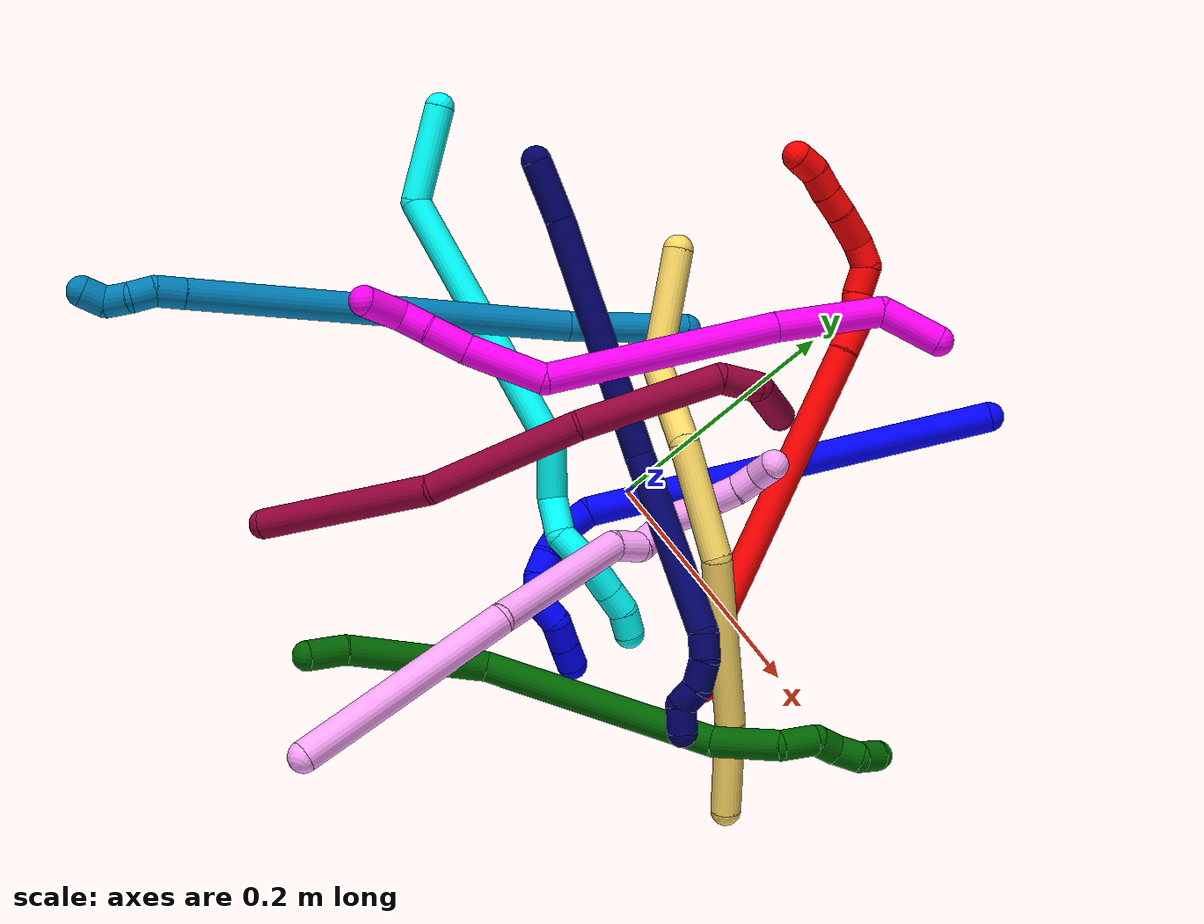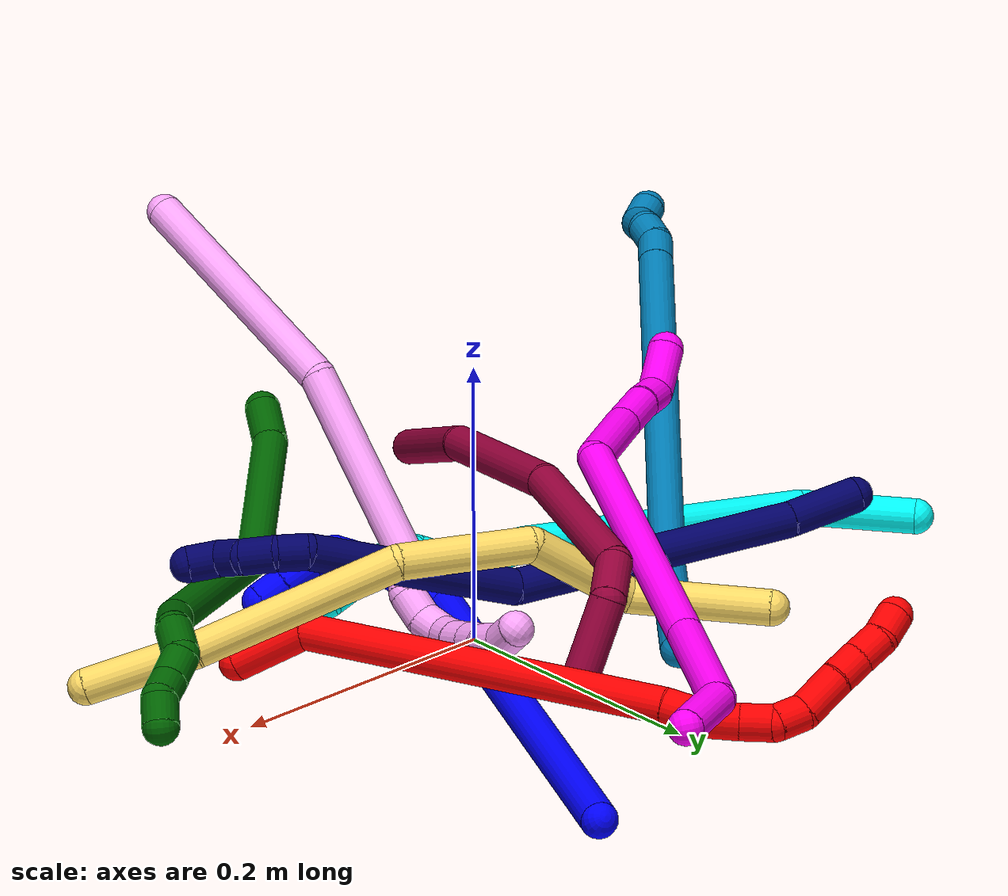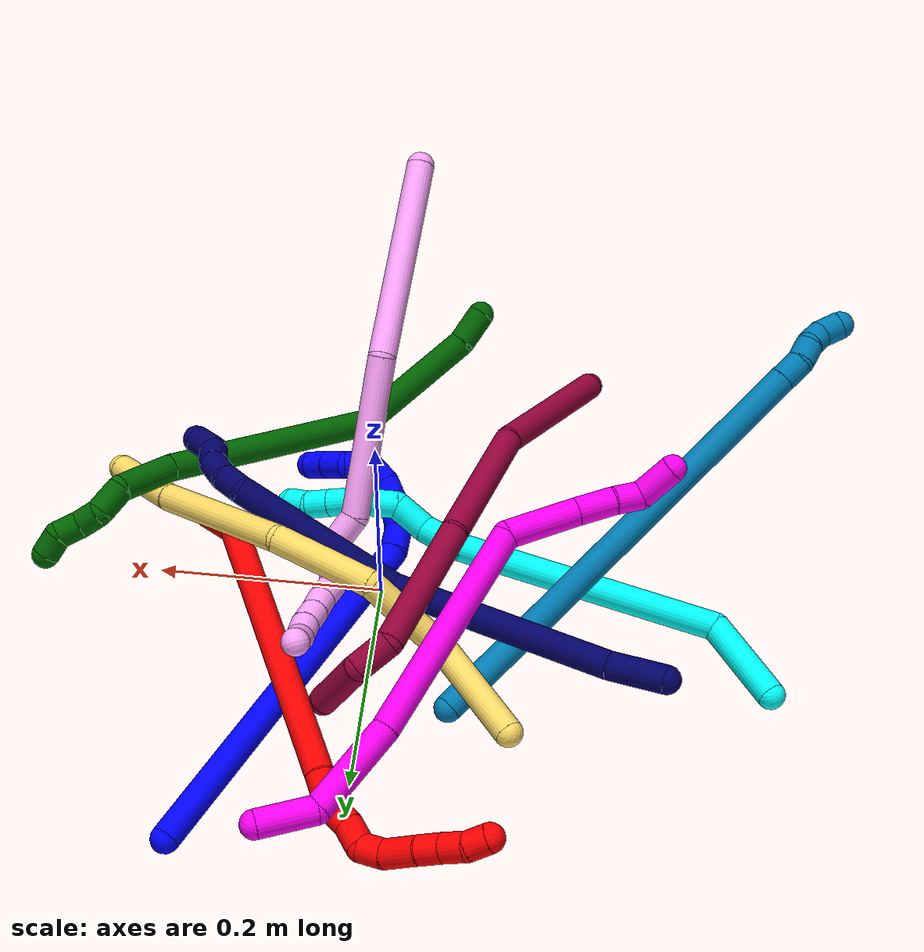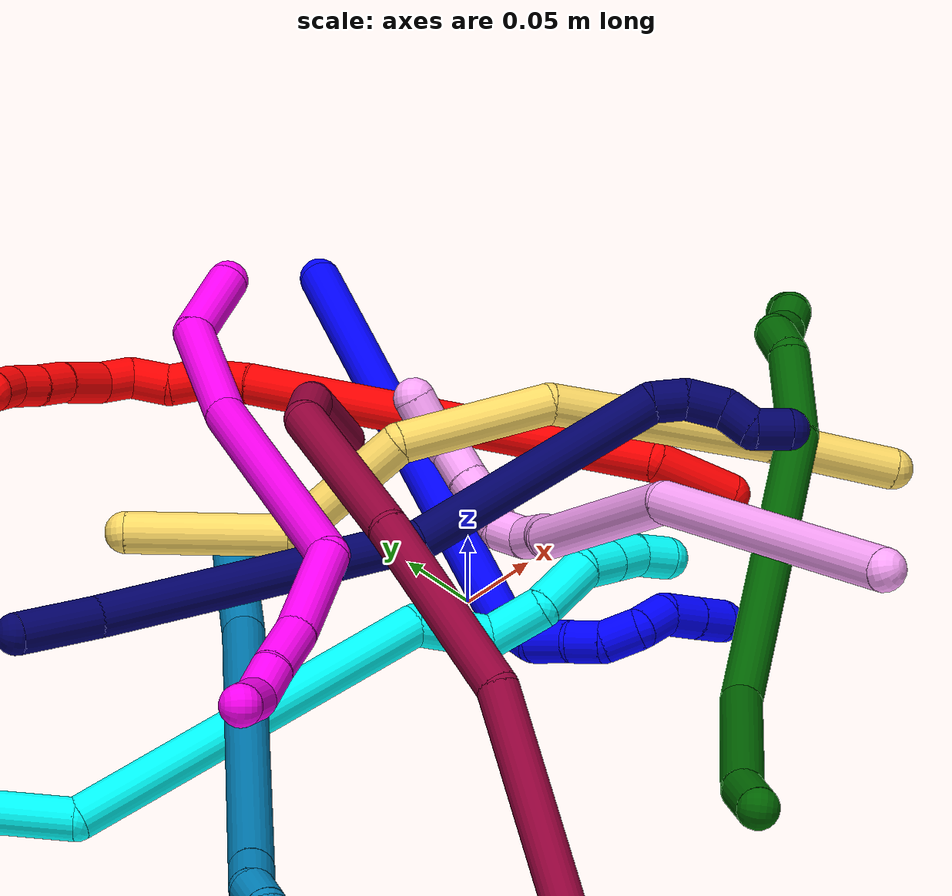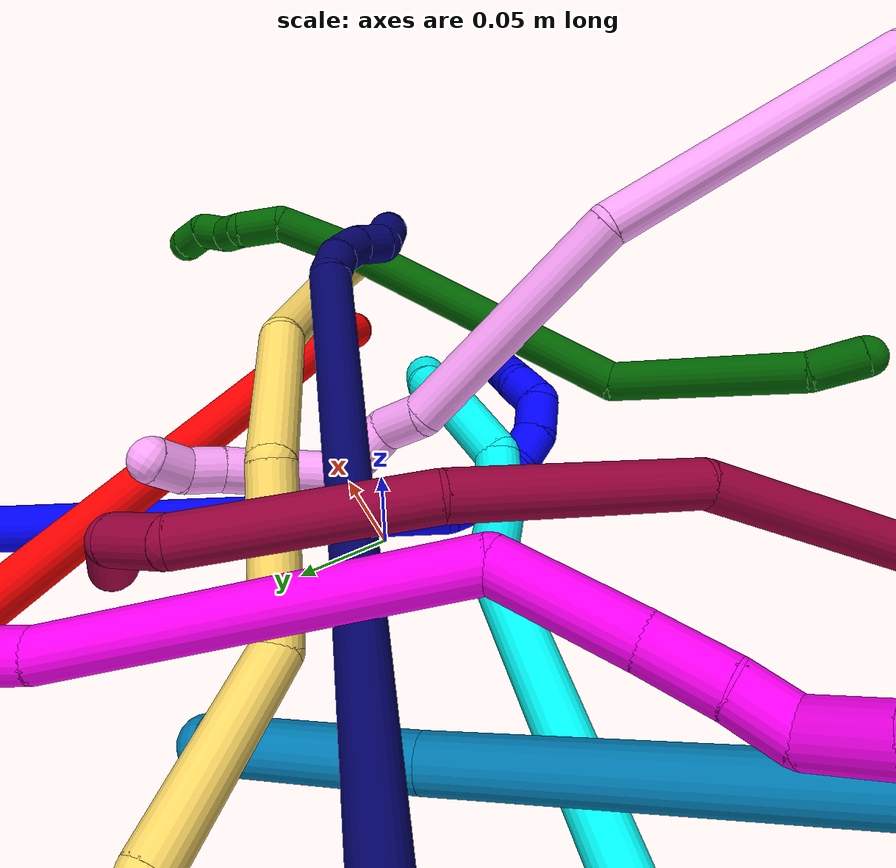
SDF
<sdf version="1.7">
 <world name="default">
  <plugin name="TubeGeneratorPlugin" filename="libtube_generator_plugin.so"/>
  <model name="photoneo_s_sensor">
   <static>1</static>
   <pose>0 0 2 1.57079 1.57079 3.14159</pose>
   <link name="link">
    <inertial><mass>0.1</mass></inertial>
    <sensor name="sensor" type="depth">
     <update_rate>30</update_rate>
     <camera>
      <horizontal_fov>1.22</horizontal_fov>
      <image><width>1920</width><height>1200</height><format>B8G8R8</format></image>
      <clip><near>0.1</near><far>4</far></clip>
      <depth_camera><output>points</output></depth_camera>
     </camera>
     <plugin name="camera_plugin" filename="libgazebo_ros_depth_camera.so">
      <baseline>0.2</baseline>
      <alwaysOn>1</alwaysOn>
      <updateRate>0.0</updateRate>
      <cameraName>camera_ir</cameraName>
      <imageTopicName>/camera/color/image_raw</imageTopicName>
      <cameraInfoTopicName>/camera/color/camera_info</cameraInfoTopicName>
      <depthImageTopicName>/camera/depth/image_raw</depthImageTopicName>
      <depthImageCameraInfoTopicName>/camera/depth/camera_info</depthImageCameraInfoTopicName>
      <pointCloudTopicName>/camera/depth/points</pointCloudTopicName>
      <frameName>fr_optical</frameName>
      <pointCloudCutoff>0.1</pointCloudCutoff>
      <pointCloudCutoffMax>2.0</pointCloudCutoffMax>
      <distortionK1>0</distortionK1>
      <distortionK2>0</distortionK2>
      <distortionK3>0</distortionK3>
      <distortionT1>0</distortionT1>
      <distortionT2>0</distortionT2>
      <CxPrime>0</CxPrime>
      <Cx>0</Cx>
      <Cy>0</Cy>
      <focalLength>0</focalLength>
      <hackBaseline>0</hackBaseline>
     </plugin>
    </sensor>
   </link>
  </model>
  <gravity>0 0 -9.8</gravity>
  <magnetic_field>6e-06 2.3e-05 -4.2e-05</magnetic_field>
  <atmosphere type="adiabatic"/>
  <physics name="default_physics" default="0" type="ode">
   <max_step_size>0.003</max_step_size>
   <real_time_factor>1</real_time_factor>
   <real_time_update_rate>1000</real_time_update_rate>
   <max_contacts>10000</max_contacts>
   <ode>
    <solver>
     <type>quick</type>
     <iters>100</iters>
     <sor>1.3</sor>
     <use_dynamic_moi_rescaling>0</use_dynamic_moi_rescaling>
    </solver>
    <constraints>
     <contact_max_correcting_vel>0</contact_max_correcting_vel>
     <contact_surface_layer>0.001</contact_surface_layer>
     <cfm>0</cfm>
     <erp>0.2</erp>
    </constraints>
   </ode>
  </physics>
  <scene><ambient>0.4 0.4 0.4 1</ambient><background>0.7 0.7 0.7 1</background><shadows>0</shadows></scene>
  <audio><device>default</device></audio>
  <spherical_coordinates>
   <surface_model>EARTH_WGS84</surface_model>
   <latitude_deg>0</latitude_deg>
   <longitude_deg>0</longitude_deg>
   <elevation>0</elevation>
   <heading_deg>0</heading_deg>
  </spherical_coordinates>
  <model name="bin">
   <static>1</static>
   <link name="bottom">
    <collision name="collision-bottom">
     <pose>0 0 -0.01 0 -0 0</pose>
     <geometry><box><size>0.8 0.6 0.02</size></box></geometry>
     <surface>
      <friction><ode><mu>100</mu><mu2>100</mu2></ode></friction>
      <contact><collide_bitmask>65535</collide_bitmask></contact>
     </surface>
    </collision>
   </link>
   <link name="west_wall">
    <collision name="collision-west_wall">
     <pose>-0.41 0 0.1 0 -0 0</pose>
     <geometry><box><size>0.02 0.6 0.2</size></box></geometry>
     <surface>
      <friction><ode><mu>100</mu><mu2>100</mu2></ode></friction>
      <contact><collide_bitmask>65535</collide_bitmask></contact>
     </surface>
    </collision>
   </link>
   <link name="east_wall">
    <collision name="collision-east_wall">
     <pose>0.41 0 0.1 0 -0 0</pose>
     <geometry><box><size>0.02 0.6 0.2</size></box></geometry>
     <surface>
      <friction><ode><mu>100</mu><mu2>100</mu2></ode></friction>
      <contact><collide_bitmask>65535</collide_bitmask></contact>
     </surface>
    </collision>
   </link>
   <link name="south_wall">
    <collision name="collision-south_wall">
     <pose>0 -0.31 0.1 0 -0 0</pose>
     <geometry><box><size>0.8 0.02 0.2</size></box></geometry>
     <surface>
      <friction><ode><mu>100</mu><mu2>100</mu2></ode></friction>
      <contact><collide_bitmask>65535</collide_bitmask></contact>
     </surface>
    </collision>
   </link>
   <link name="north_wall">
    <collision name="collision-north_wall">
     <pose>0 0.31 0.1 0 -0 0</pose>
     <geometry><box><size>0.8 0.02 0.2</size></box></geometry>
     <surface>
      <friction><ode><mu>100</mu><mu2>100</mu2></ode></friction>
      <contact><collide_bitmask>65535</collide_bitmask></contact>
     </surface>
    </collision>
   </link>
  </model>
  <model name="1">
   <static>0</static>
   <link name="1">
    <collision name="collision-cylinder-e_1_1_4">
     <pose>-0.064429 -0.074584 -0.139258 2.64989 -0.387251 -1.32662</pose>
     <geometry><cylinder><radius>0.0125</radius><length>0.341213</length></cylinder></geometry>
     <surface>
      <friction><ode><mu>1.16</mu><mu2>1.16</mu2><slip1>0</slip1><slip2>0</slip2></ode></friction>
      <contact><ode><kp>1e+06</kp><kd>1</kd><max_vel>0</max_vel><min_depth>0.001</min_depth></ode></contact>
     </surface>
    </collision>
    <visual name="visual-cylinder-e_1_1_4">
     <pose>-0.064429 -0.074584 -0.139258 2.64989 -0.387251 -1.32662</pose>
     <geometry><cylinder><radius>0.0125</radius><length>0.341213</length></cylinder></geometry>
     <material><ambient>0 0 1 1</ambient></material>
    </visual>
    <collision name="collision-cylinder-e_2_4_5">
     <pose>-0.129223 -0.157543 -0.288476 2.44243 -0.028118 -0.077096</pose>
     <geometry><cylinder><radius>0.0125</radius><length>0.026037</length></cylinder></geometry>
     <surface>
      <friction><ode><mu>1.16</mu><mu2>1.16</mu2><slip1>0</slip1><slip2>0</slip2></ode></friction>
      <contact><ode><kp>1e+06</kp><kd>1</kd><max_vel>0</max_vel><min_depth>0.001</min_depth></ode></contact>
     </surface>
    </collision>
    <visual name="visual-cylinder-e_2_4_5">
     <pose>-0.129223 -0.157543 -0.288476 2.44243 -0.028118 -0.077096</pose>
     <geometry><cylinder><radius>0.0125</radius><length>0.026037</length></cylinder></geometry>
     <material><ambient>0 0 1 1</ambient></material>
    </visual>
    <collision name="collision-cylinder-e_3_5_6">
     <pose>-0.127982 -0.177607 -0.303522 1.98121 0.125386 0.190968</pose>
     <geometry><cylinder><radius>0.0125</radius><length>0.025697</length></cylinder></geometry>
     <surface>
      <friction><ode><mu>1.16</mu><mu2>1.16</mu2><slip1>0</slip1><slip2>0</slip2></ode></friction>
      <contact><ode><kp>1e+06</kp><kd>1</kd><max_vel>0</max_vel><min_depth>0.001</min_depth></ode></contact>
     </surface>
    </collision>
    <visual name="visual-cylinder-e_3_5_6">
     <pose>-0.127982 -0.177607 -0.303522 1.98121 0.125386 0.190968</pose>
     <geometry><cylinder><radius>0.0125</radius><length>0.025697</length></cylinder></geometry>
     <material><ambient>0 0 1 1</ambient></material>
    </visual>
    <collision name="collision-cylinder-e_4_6_7">
     <pose>-0.122667 -0.197791 -0.312906 2.03916 0.371494 0.593283</pose>
     <geometry><cylinder><radius>0.0125</radius><length>0.020435</length></cylinder></geometry>
     <surface>
      <friction><ode><mu>1.16</mu><mu2>1.16</mu2><slip1>0</slip1><slip2>0</slip2></ode></friction>
      <contact><ode><kp>1e+06</kp><kd>1</kd><max_vel>0</max_vel><min_depth>0.001</min_depth></ode></contact>
     </surface>
    </collision>
    <visual name="visual-cylinder-e_4_6_7">
     <pose>-0.122667 -0.197791 -0.312906 2.03916 0.371494 0.593283</pose>
     <geometry><cylinder><radius>0.0125</radius><length>0.020435</length></cylinder></geometry>
     <material><ambient>0 0 1 1</ambient></material>
    </visual>
    <collision name="collision-cylinder-e_5_7_8">
     <pose>-0.112657 -0.215395 -0.317573 1.61126 0.60477 0.628167</pose>
     <geometry><cylinder><radius>0.0125</radius><length>0.022163</length></cylinder></geometry>
     <surface>
      <friction><ode><mu>1.16</mu><mu2>1.16</mu2><slip1>0</slip1><slip2>0</slip2></ode></friction>
      <contact><ode><kp>1e+06</kp><kd>1</kd><max_vel>0</max_vel><min_depth>0.001</min_depth></ode></contact>
     </surface>
    </collision>
    <visual name="visual-cylinder-e_5_7_8">
     <pose>-0.112657 -0.215395 -0.317573 1.61126 0.60477 0.628167</pose>
     <geometry><cylinder><radius>0.0125</radius><length>0.022163</length></cylinder></geometry>
     <material><ambient>0 0 1 1</ambient></material>
    </visual>
    <collision name="collision-cylinder-e_6_8_9">
     <pose>-0.096292 -0.22674 -0.315622 0.767044 1.26096 0.572798</pose>
     <geometry><cylinder><radius>0.0125</radius><length>0.021134</length></cylinder></geometry>
     <surface>
      <friction><ode><mu>1.16</mu><mu2>1.16</mu2><slip1>0</slip1><slip2>0</slip2></ode></friction>
      <contact><ode><kp>1e+06</kp><kd>1</kd><max_vel>0</max_vel><min_depth>0.001</min_depth></ode></contact>
     </surface>
    </collision>
    <visual name="visual-cylinder-e_6_8_9">
     <pose>-0.096292 -0.22674 -0.315622 0.767044 1.26096 0.572798</pose>
     <geometry><cylinder><radius>0.0125</radius><length>0.021134</length></cylinder></geometry>
     <material><ambient>0 0 1 1</ambient></material>
    </visual>
    <collision name="collision-cylinder-e_7_9_10">
     <pose>-0.075349 -0.229966 -0.316458 2.83745 1.27565 2.7338</pose>
     <geometry><cylinder><radius>0.0125</radius><length>0.022742</length></cylinder></geometry>
     <surface>
      <friction><ode><mu>1.16</mu><mu2>1.16</mu2><slip1>0</slip1><slip2>0</slip2></ode></friction>
      <contact><ode><kp>1e+06</kp><kd>1</kd><max_vel>0</max_vel><min_depth>0.001</min_depth></ode></contact>
     </surface>
    </collision>
    <visual name="visual-cylinder-e_7_9_10">
     <pose>-0.075349 -0.229966 -0.316458 2.83745 1.27565 2.7338</pose>
     <geometry><cylinder><radius>0.0125</radius><length>0.022742</length></cylinder></geometry>
     <material><ambient>0 0 1 1</ambient></material>
    </visual>
    <collision name="collision-cylinder-e_8_10_2">
     <pose>-0.054571 -0.231748 -0.32231 2.85608 1.29414 2.76563</pose>
     <geometry><cylinder><radius>0.0125</radius><length>0.020578</length></cylinder></geometry>
     <surface>
      <friction><ode><mu>1.16</mu><mu2>1.16</mu2><slip1>0</slip1><slip2>0</slip2></ode></friction>
      <contact><ode><kp>1e+06</kp><kd>1</kd><max_vel>0</max_vel><min_depth>0.001</min_depth></ode></contact>
     </surface>
    </collision>
    <visual name="visual-cylinder-e_8_10_2">
     <pose>-0.054571 -0.231748 -0.32231 2.85608 1.29414 2.76563</pose>
     <geometry><cylinder><radius>0.0125</radius><length>0.020578</length></cylinder></geometry>
     <material><ambient>0 0 1 1</ambient></material>
    </visual>
    <collision name="collision-sphere-2">
     <pose>-0.044673 -0.23254 -0.325007 0 -0 0</pose>
     <geometry><sphere><radius>0.0125</radius></sphere></geometry>
     <surface>
      <friction><ode><mu>1.16</mu><mu2>1.16</mu2><slip1>0</slip1><slip2>0</slip2></ode></friction>
      <contact><ode><kp>1e+06</kp><kd>1</kd><max_vel>0</max_vel><min_depth>0.001</min_depth></ode></contact>
     </surface>
    </collision>
    <visual name="visual-sphere-2">
     <pose>-0.044673 -0.23254 -0.325007 0 -0 0</pose>
     <geometry><sphere><radius>0.0125</radius></sphere></geometry>
     <material><ambient>0 0 1 1</ambient></material>
    </visual>
    <collision name="collision-sphere-10">
     <pose>-0.064469 -0.230957 -0.319614 0 -0 0</pose>
     <geometry><sphere><radius>0.0125</radius></sphere></geometry>
     <surface>
      <friction><ode><mu>1.16</mu><mu2>1.16</mu2><slip1>0</slip1><slip2>0</slip2></ode></friction>
      <contact><ode><kp>1e+06</kp><kd>1</kd><max_vel>0</max_vel><min_depth>0.001</min_depth></ode></contact>
     </surface>
    </collision>
    <visual name="visual-sphere-10">
     <pose>-0.064469 -0.230957 -0.319614 0 -0 0</pose>
     <geometry><sphere><radius>0.0125</radius></sphere></geometry>
     <material><ambient>0 0 1 1</ambient></material>
    </visual>
    <collision name="collision-sphere-9">
     <pose>-0.086228 -0.228976 -0.313302 0 -0 0</pose>
     <geometry><sphere><radius>0.0125</radius></sphere></geometry>
     <surface>
      <friction><ode><mu>1.16</mu><mu2>1.16</mu2><slip1>0</slip1><slip2>0</slip2></ode></friction>
      <contact><ode><kp>1e+06</kp><kd>1</kd><max_vel>0</max_vel><min_depth>0.001</min_depth></ode></contact>
     </surface>
    </collision>
    <visual name="visual-sphere-9">
     <pose>-0.086228 -0.228976 -0.313302 0 -0 0</pose>
     <geometry><sphere><radius>0.0125</radius></sphere></geometry>
     <material><ambient>0 0 1 1</ambient></material>
    </visual>
    <collision name="collision-sphere-4">
     <pose>-0.128857 -0.149168 -0.278516 0 -0 0</pose>
     <geometry><sphere><radius>0.0125</radius></sphere></geometry>
     <surface>
      <friction><ode><mu>1.16</mu><mu2>1.16</mu2><slip1>0</slip1><slip2>0</slip2></ode></friction>
      <contact><ode><kp>1e+06</kp><kd>1</kd><max_vel>0</max_vel><min_depth>0.001</min_depth></ode></contact>
     </surface>
    </collision>
    <visual name="visual-sphere-4">
     <pose>-0.128857 -0.149168 -0.278516 0 -0 0</pose>
     <geometry><sphere><radius>0.0125</radius></sphere></geometry>
     <material><ambient>0 0 1 1</ambient></material>
    </visual>
    <collision name="collision-sphere-1">
     <geometry><sphere><radius>0.0125</radius></sphere></geometry>
     <surface>
      <friction><ode><mu>1.16</mu><mu2>1.16</mu2><slip1>0</slip1><slip2>0</slip2></ode></friction>
      <contact><ode><kp>1e+06</kp><kd>1</kd><max_vel>0</max_vel><min_depth>0.001</min_depth></ode></contact>
     </surface>
    </collision>
    <visual name="visual-sphere-1">
     <geometry><sphere><radius>0.0125</radius></sphere></geometry>
     <material><ambient>0 0 1 1</ambient></material>
    </visual>
    <collision name="collision-sphere-8">
     <pose>-0.106356 -0.224504 -0.317942 0 -0 0</pose>
     <geometry><sphere><radius>0.0125</radius></sphere></geometry>
     <surface>
      <friction><ode><mu>1.16</mu><mu2>1.16</mu2><slip1>0</slip1><slip2>0</slip2></ode></friction>
      <contact><ode><kp>1e+06</kp><kd>1</kd><max_vel>0</max_vel><min_depth>0.001</min_depth></ode></contact>
     </surface>
    </collision>
    <visual name="visual-sphere-8">
     <pose>-0.106356 -0.224504 -0.317942 0 -0 0</pose>
     <geometry><sphere><radius>0.0125</radius></sphere></geometry>
     <material><ambient>0 0 1 1</ambient></material>
    </visual>
    <collision name="collision-sphere-5">
     <pose>-0.129589 -0.165918 -0.298436 0 -0 0</pose>
     <geometry><sphere><radius>0.0125</radius></sphere></geometry>
     <surface>
      <friction><ode><mu>1.16</mu><mu2>1.16</mu2><slip1>0</slip1><slip2>0</slip2></ode></friction>
      <contact><ode><kp>1e+06</kp><kd>1</kd><max_vel>0</max_vel><min_depth>0.001</min_depth></ode></contact>
     </surface>
    </collision>
    <visual name="visual-sphere-5">
     <pose>-0.129589 -0.165918 -0.298436 0 -0 0</pose>
     <geometry><sphere><radius>0.0125</radius></sphere></geometry>
     <material><ambient>0 0 1 1</ambient></material>
    </visual>
    <collision name="collision-sphere-6">
     <pose>-0.126376 -0.189296 -0.308608 0 -0 0</pose>
     <geometry><sphere><radius>0.0125</radius></sphere></geometry>
     <surface>
      <friction><ode><mu>1.16</mu><mu2>1.16</mu2><slip1>0</slip1><slip2>0</slip2></ode></friction>
      <contact><ode><kp>1e+06</kp><kd>1</kd><max_vel>0</max_vel><min_depth>0.001</min_depth></ode></contact>
     </surface>
    </collision>
    <visual name="visual-sphere-6">
     <pose>-0.126376 -0.189296 -0.308608 0 -0 0</pose>
     <geometry><sphere><radius>0.0125</radius></sphere></geometry>
     <material><ambient>0 0 1 1</ambient></material>
    </visual>
    <collision name="collision-sphere-7">
     <pose>-0.118957 -0.206286 -0.317204 0 -0 0</pose>
     <geometry><sphere><radius>0.0125</radius></sphere></geometry>
     <surface>
      <friction><ode><mu>1.16</mu><mu2>1.16</mu2><slip1>0</slip1><slip2>0</slip2></ode></friction>
      <contact><ode><kp>1e+06</kp><kd>1</kd><max_vel>0</max_vel><min_depth>0.001</min_depth></ode></contact>
     </surface>
    </collision>
    <visual name="visual-sphere-7">
     <pose>-0.118957 -0.206286 -0.317204 0 -0 0</pose>
     <geometry><sphere><radius>0.0125</radius></sphere></geometry>
     <material><ambient>0 0 1 1</ambient></material>
    </visual>
    <inertial>
     <pose>-0.077025 -0.115443 -0.19352 0 -0 0</pose>
     <mass>0.5</mass>
     <inertia>
      <ixx>-0.002237</ixx>
      <ixy>0</ixy>
      <ixz>0</ixz>
      <iyy>-0.003133</iyy>
      <iyz>0</iyz>
      <izz>0.002683</izz>
     </inertia>
    </inertial>
   </link>
   <pose>0.140667 0.271674 0.01149 -0.90339 0.404856 -0.023743</pose>
  </model>
  <model name="2">
   <static>0</static>
   <link name="2">
    <collision name="collision-cylinder-e_1_1_4">
     <pose>-0.016876 0.004932 0.018583 -0.259427 -0.720386 0.098179</pose>
     <geometry><cylinder><radius>0.0125</radius><length>0.051165</length></cylinder></geometry>
     <surface>
      <friction><ode><mu>1.16</mu><mu2>1.16</mu2><slip1>0</slip1><slip2>0</slip2></ode></friction>
      <contact><ode><kp>1e+06</kp><kd>1</kd><max_vel>0</max_vel><min_depth>0.001</min_depth></ode></contact>
     </surface>
    </collision>
    <visual name="visual-cylinder-e_1_1_4">
     <pose>-0.016876 0.004932 0.018583 -0.259427 -0.720386 0.098179</pose>
     <geometry><cylinder><radius>0.0125</radius><length>0.051165</length></cylinder></geometry>
     <material><ambient>1 0 0 1</ambient></material>
    </visual>
    <collision name="collision-cylinder-e_2_4_5">
     <pose>-0.048212 0.05517 0.156551 -0.362705 -0.112759 0.020698</pose>
     <geometry><cylinder><radius>0.0125</radius><length>0.257017</length></cylinder></geometry>
     <surface>
      <friction><ode><mu>1.16</mu><mu2>1.16</mu2><slip1>0</slip1><slip2>0</slip2></ode></friction>
      <contact><ode><kp>1e+06</kp><kd>1</kd><max_vel>0</max_vel><min_depth>0.001</min_depth></ode></contact>
     </surface>
    </collision>
    <visual name="visual-cylinder-e_2_4_5">
     <pose>-0.048212 0.05517 0.156551 -0.362705 -0.112759 0.020698</pose>
     <geometry><cylinder><radius>0.0125</radius><length>0.257017</length></cylinder></geometry>
     <material><ambient>1 0 0 1</ambient></material>
    </visual>
    <collision name="collision-cylinder-e_3_5_6">
     <pose>-0.06301 0.106724 0.289666 -0.427065 -0.022391 0.004856</pose>
     <geometry><cylinder><radius>0.0125</radius><length>0.030178</length></cylinder></geometry>
     <surface>
      <friction><ode><mu>1.16</mu><mu2>1.16</mu2><slip1>0</slip1><slip2>0</slip2></ode></friction>
      <contact><ode><kp>1e+06</kp><kd>1</kd><max_vel>0</max_vel><min_depth>0.001</min_depth></ode></contact>
     </surface>
    </collision>
    <visual name="visual-cylinder-e_3_5_6">
     <pose>-0.06301 0.106724 0.289666 -0.427065 -0.022391 0.004856</pose>
     <geometry><cylinder><radius>0.0125</radius><length>0.030178</length></cylinder></geometry>
     <material><ambient>1 0 0 1</ambient></material>
    </visual>
    <collision name="collision-cylinder-e_4_6_7">
     <pose>-0.066364 0.120248 0.310512 -0.796496 -0.288137 0.121922</pose>
     <geometry><cylinder><radius>0.0125</radius><length>0.021228</length></cylinder></geometry>
     <surface>
      <friction><ode><mu>1.16</mu><mu2>1.16</mu2><slip1>0</slip1><slip2>0</slip2></ode></friction>
      <contact><ode><kp>1e+06</kp><kd>1</kd><max_vel>0</max_vel><min_depth>0.001</min_depth></ode></contact>
     </surface>
    </collision>
    <visual name="visual-cylinder-e_4_6_7">
     <pose>-0.066364 0.120248 0.310512 -0.796496 -0.288137 0.121922</pose>
     <geometry><cylinder><radius>0.0125</radius><length>0.021228</length></cylinder></geometry>
     <material><ambient>1 0 0 1</ambient></material>
    </visual>
    <collision name="collision-cylinder-e_5_7_8">
     <pose>-0.072757 0.131981 0.328296 -0.395834 -0.284162 0.057357</pose>
     <geometry><cylinder><radius>0.0125</radius><length>0.024093</length></cylinder></geometry>
     <surface>
      <friction><ode><mu>1.16</mu><mu2>1.16</mu2><slip1>0</slip1><slip2>0</slip2></ode></friction>
      <contact><ode><kp>1e+06</kp><kd>1</kd><max_vel>0</max_vel><min_depth>0.001</min_depth></ode></contact>
     </surface>
    </collision>
    <visual name="visual-cylinder-e_5_7_8">
     <pose>-0.072757 0.131981 0.328296 -0.395834 -0.284162 0.057357</pose>
     <geometry><cylinder><radius>0.0125</radius><length>0.024093</length></cylinder></geometry>
     <material><ambient>1 0 0 1</ambient></material>
    </visual>
    <collision name="collision-cylinder-e_6_8_9">
     <pose>-0.08317 0.143191 0.34297 -1.0354 -0.730774 0.429045</pose>
     <geometry><cylinder><radius>0.0125</radius><length>0.021082</length></cylinder></geometry>
     <surface>
      <friction><ode><mu>1.16</mu><mu2>1.16</mu2><slip1>0</slip1><slip2>0</slip2></ode></friction>
      <contact><ode><kp>1e+06</kp><kd>1</kd><max_vel>0</max_vel><min_depth>0.001</min_depth></ode></contact>
     </surface>
    </collision>
    <visual name="visual-cylinder-e_6_8_9">
     <pose>-0.08317 0.143191 0.34297 -1.0354 -0.730774 0.429045</pose>
     <geometry><cylinder><radius>0.0125</radius><length>0.021082</length></cylinder></geometry>
     <material><ambient>1 0 0 1</ambient></material>
    </visual>
    <collision name="collision-cylinder-e_7_9_10">
     <pose>-0.104763 0.156543 0.349837 -1.16167 -1.11178 0.774353</pose>
     <geometry><cylinder><radius>0.0125</radius><length>0.032479</length></cylinder></geometry>
     <surface>
      <friction><ode><mu>1.16</mu><mu2>1.16</mu2><slip1>0</slip1><slip2>0</slip2></ode></friction>
      <contact><ode><kp>1e+06</kp><kd>1</kd><max_vel>0</max_vel><min_depth>0.001</min_depth></ode></contact>
     </surface>
    </collision>
    <visual name="visual-cylinder-e_7_9_10">
     <pose>-0.104763 0.156543 0.349837 -1.16167 -1.11178 0.774353</pose>
     <geometry><cylinder><radius>0.0125</radius><length>0.032479</length></cylinder></geometry>
     <material><ambient>1 0 0 1</ambient></material>
    </visual>
    <collision name="collision-cylinder-e_8_10_11">
     <pose>-0.128431 0.168381 0.354059 -1.31667 -1.03481 0.829318</pose>
     <geometry><cylinder><radius>0.0125</radius><length>0.021189</length></cylinder></geometry>
     <surface>
      <friction><ode><mu>1.16</mu><mu2>1.16</mu2><slip1>0</slip1><slip2>0</slip2></ode></friction>
      <contact><ode><kp>1e+06</kp><kd>1</kd><max_vel>0</max_vel><min_depth>0.001</min_depth></ode></contact>
     </surface>
    </collision>
    <visual name="visual-cylinder-e_8_10_11">
     <pose>-0.128431 0.168381 0.354059 -1.31667 -1.03481 0.829318</pose>
     <geometry><cylinder><radius>0.0125</radius><length>0.021189</length></cylinder></geometry>
     <material><ambient>1 0 0 1</ambient></material>
    </visual>
    <collision name="collision-cylinder-e_9_11_12">
     <pose>-0.146867 0.178435 0.357588 -1.14786 -1.0555 0.720803</pose>
     <geometry><cylinder><radius>0.0125</radius><length>0.02144</length></cylinder></geometry>
     <surface>
      <friction><ode><mu>1.16</mu><mu2>1.16</mu2><slip1>0</slip1><slip2>0</slip2></ode></friction>
      <contact><ode><kp>1e+06</kp><kd>1</kd><max_vel>0</max_vel><min_depth>0.001</min_depth></ode></contact>
     </surface>
    </collision>
    <visual name="visual-cylinder-e_9_11_12">
     <pose>-0.146867 0.178435 0.357588 -1.14786 -1.0555 0.720803</pose>
     <geometry><cylinder><radius>0.0125</radius><length>0.02144</length></cylinder></geometry>
     <material><ambient>1 0 0 1</ambient></material>
    </visual>
    <collision name="collision-cylinder-e_10_12_2">
     <pose>-0.165248 0.187511 0.358648 -1.82533 -1.11829 1.3609</pose>
     <geometry><cylinder><radius>0.0125</radius><length>0.020131</length></cylinder></geometry>
     <surface>
      <friction><ode><mu>1.16</mu><mu2>1.16</mu2><slip1>0</slip1><slip2>0</slip2></ode></friction>
      <contact><ode><kp>1e+06</kp><kd>1</kd><max_vel>0</max_vel><min_depth>0.001</min_depth></ode></contact>
     </surface>
    </collision>
    <visual name="visual-cylinder-e_10_12_2">
     <pose>-0.165248 0.187511 0.358648 -1.82533 -1.11829 1.3609</pose>
     <geometry><cylinder><radius>0.0125</radius><length>0.020131</length></cylinder></geometry>
     <material><ambient>1 0 0 1</ambient></material>
    </visual>
    <collision name="collision-sphere-2">
     <pose>-0.1743 0.19177 0.35754 0 -0 0</pose>
     <geometry><sphere><radius>0.0125</radius></sphere></geometry>
     <surface>
      <friction><ode><mu>1.16</mu><mu2>1.16</mu2><slip1>0</slip1><slip2>0</slip2></ode></friction>
      <contact><ode><kp>1e+06</kp><kd>1</kd><max_vel>0</max_vel><min_depth>0.001</min_depth></ode></contact>
     </surface>
    </collision>
    <visual name="visual-sphere-2">
     <pose>-0.1743 0.19177 0.35754 0 -0 0</pose>
     <geometry><sphere><radius>0.0125</radius></sphere></geometry>
     <material><ambient>1 0 0 1</ambient></material>
    </visual>
    <collision name="collision-sphere-12">
     <pose>-0.156195 0.183252 0.359756 0 -0 0</pose>
     <geometry><sphere><radius>0.0125</radius></sphere></geometry>
     <surface>
      <friction><ode><mu>1.16</mu><mu2>1.16</mu2><slip1>0</slip1><slip2>0</slip2></ode></friction>
      <contact><ode><kp>1e+06</kp><kd>1</kd><max_vel>0</max_vel><min_depth>0.001</min_depth></ode></contact>
     </surface>
    </collision>
    <visual name="visual-sphere-12">
     <pose>-0.156195 0.183252 0.359756 0 -0 0</pose>
     <geometry><sphere><radius>0.0125</radius></sphere></geometry>
     <material><ambient>1 0 0 1</ambient></material>
    </visual>
    <collision name="collision-sphere-11">
     <pose>-0.137539 0.173618 0.355419 0 -0 0</pose>
     <geometry><sphere><radius>0.0125</radius></sphere></geometry>
     <surface>
      <friction><ode><mu>1.16</mu><mu2>1.16</mu2><slip1>0</slip1><slip2>0</slip2></ode></friction>
      <contact><ode><kp>1e+06</kp><kd>1</kd><max_vel>0</max_vel><min_depth>0.001</min_depth></ode></contact>
     </surface>
    </collision>
    <visual name="visual-sphere-11">
     <pose>-0.137539 0.173618 0.355419 0 -0 0</pose>
     <geometry><sphere><radius>0.0125</radius></sphere></geometry>
     <material><ambient>1 0 0 1</ambient></material>
    </visual>
    <collision name="collision-sphere-10">
     <pose>-0.119322 0.163144 0.352699 0 -0 0</pose>
     <geometry><sphere><radius>0.0125</radius></sphere></geometry>
     <surface>
      <friction><ode><mu>1.16</mu><mu2>1.16</mu2><slip1>0</slip1><slip2>0</slip2></ode></friction>
      <contact><ode><kp>1e+06</kp><kd>1</kd><max_vel>0</max_vel><min_depth>0.001</min_depth></ode></contact>
     </surface>
    </collision>
    <visual name="visual-sphere-10">
     <pose>-0.119322 0.163144 0.352699 0 -0 0</pose>
     <geometry><sphere><radius>0.0125</radius></sphere></geometry>
     <material><ambient>1 0 0 1</ambient></material>
    </visual>
    <collision name="collision-sphere-9">
     <pose>-0.090205 0.149942 0.346975 0 -0 0</pose>
     <geometry><sphere><radius>0.0125</radius></sphere></geometry>
     <surface>
      <friction><ode><mu>1.16</mu><mu2>1.16</mu2><slip1>0</slip1><slip2>0</slip2></ode></friction>
      <contact><ode><kp>1e+06</kp><kd>1</kd><max_vel>0</max_vel><min_depth>0.001</min_depth></ode></contact>
     </surface>
    </collision>
    <visual name="visual-sphere-9">
     <pose>-0.090205 0.149942 0.346975 0 -0 0</pose>
     <geometry><sphere><radius>0.0125</radius></sphere></geometry>
     <material><ambient>1 0 0 1</ambient></material>
    </visual>
    <collision name="collision-sphere-4">
     <pose>-0.033752 0.009864 0.037166 0 -0 0</pose>
     <geometry><sphere><radius>0.0125</radius></sphere></geometry>
     <surface>
      <friction><ode><mu>1.16</mu><mu2>1.16</mu2><slip1>0</slip1><slip2>0</slip2></ode></friction>
      <contact><ode><kp>1e+06</kp><kd>1</kd><max_vel>0</max_vel><min_depth>0.001</min_depth></ode></contact>
     </surface>
    </collision>
    <visual name="visual-sphere-4">
     <pose>-0.033752 0.009864 0.037166 0 -0 0</pose>
     <geometry><sphere><radius>0.0125</radius></sphere></geometry>
     <material><ambient>1 0 0 1</ambient></material>
    </visual>
    <collision name="collision-sphere-1">
     <geometry><sphere><radius>0.0125</radius></sphere></geometry>
     <surface>
      <friction><ode><mu>1.16</mu><mu2>1.16</mu2><slip1>0</slip1><slip2>0</slip2></ode></friction>
      <contact><ode><kp>1e+06</kp><kd>1</kd><max_vel>0</max_vel><min_depth>0.001</min_depth></ode></contact>
     </surface>
    </collision>
    <visual name="visual-sphere-1">
     <geometry><sphere><radius>0.0125</radius></sphere></geometry>
     <material><ambient>1 0 0 1</ambient></material>
    </visual>
    <collision name="collision-sphere-8">
     <pose>-0.076134 0.13644 0.338965 0 -0 0</pose>
     <geometry><sphere><radius>0.0125</radius></sphere></geometry>
     <surface>
      <friction><ode><mu>1.16</mu><mu2>1.16</mu2><slip1>0</slip1><slip2>0</slip2></ode></friction>
      <contact><ode><kp>1e+06</kp><kd>1</kd><max_vel>0</max_vel><min_depth>0.001</min_depth></ode></contact>
     </surface>
    </collision>
    <visual name="visual-sphere-8">
     <pose>-0.076134 0.13644 0.338965 0 -0 0</pose>
     <geometry><sphere><radius>0.0125</radius></sphere></geometry>
     <material><ambient>1 0 0 1</ambient></material>
    </visual>
    <collision name="collision-sphere-5">
     <pose>-0.062672 0.100476 0.275936 0 -0 0</pose>
     <geometry><sphere><radius>0.0125</radius></sphere></geometry>
     <surface>
      <friction><ode><mu>1.16</mu><mu2>1.16</mu2><slip1>0</slip1><slip2>0</slip2></ode></friction>
      <contact><ode><kp>1e+06</kp><kd>1</kd><max_vel>0</max_vel><min_depth>0.001</min_depth></ode></contact>
     </surface>
    </collision>
    <visual name="visual-sphere-5">
     <pose>-0.062672 0.100476 0.275936 0 -0 0</pose>
     <geometry><sphere><radius>0.0125</radius></sphere></geometry>
     <material><ambient>1 0 0 1</ambient></material>
    </visual>
    <collision name="collision-sphere-6">
     <pose>-0.063347 0.112972 0.303396 0 -0 0</pose>
     <geometry><sphere><radius>0.0125</radius></sphere></geometry>
     <surface>
      <friction><ode><mu>1.16</mu><mu2>1.16</mu2><slip1>0</slip1><slip2>0</slip2></ode></friction>
      <contact><ode><kp>1e+06</kp><kd>1</kd><max_vel>0</max_vel><min_depth>0.001</min_depth></ode></contact>
     </surface>
    </collision>
    <visual name="visual-sphere-6">
     <pose>-0.063347 0.112972 0.303396 0 -0 0</pose>
     <geometry><sphere><radius>0.0125</radius></sphere></geometry>
     <material><ambient>1 0 0 1</ambient></material>
    </visual>
    <collision name="collision-sphere-7">
     <pose>-0.06938 0.127523 0.317627 0 -0 0</pose>
     <geometry><sphere><radius>0.0125</radius></sphere></geometry>
     <surface>
      <friction><ode><mu>1.16</mu><mu2>1.16</mu2><slip1>0</slip1><slip2>0</slip2></ode></friction>
      <contact><ode><kp>1e+06</kp><kd>1</kd><max_vel>0</max_vel><min_depth>0.001</min_depth></ode></contact>
     </surface>
    </collision>
    <visual name="visual-sphere-7">
     <pose>-0.06938 0.127523 0.317627 0 -0 0</pose>
     <geometry><sphere><radius>0.0125</radius></sphere></geometry>
     <material><ambient>1 0 0 1</ambient></material>
    </visual>
    <inertial>
     <pose>-0.065341 0.085313 0.210822 0 -0 0</pose>
     <mass>0.5</mass>
     <inertia>
      <ixx>0.001457</ixx>
      <ixy>0</ixy>
      <ixz>0</ixz>
      <iyy>0.00141</iyy>
      <iyz>0</iyz>
      <izz>-0.000306</izz>
     </inertia>
    </inertial>
   </link>
   <pose>0.164983 -0.054693 0.017108 -1.42274 0.921796 0.209434</pose>
  </model>
  <model name="3">
   <static>0</static>
   <link name="3">
    <collision name="collision-cylinder-e_1_1_4">
     <pose>0.005523 -0.03026 -0.026968 2.29874 0.135416 0.300265</pose>
     <geometry><cylinder><radius>0.0125</radius><length>0.081816</length></cylinder></geometry>
     <surface>
      <friction><ode><mu>1.16</mu><mu2>1.16</mu2><slip1>0</slip1><slip2>0</slip2></ode></friction>
      <contact><ode><kp>1e+06</kp><kd>1</kd><max_vel>0</max_vel><min_depth>0.001</min_depth></ode></contact>
     </surface>
    </collision>
    <visual name="visual-cylinder-e_1_1_4">
     <pose>0.005523 -0.03026 -0.026968 2.29874 0.135416 0.300265</pose>
     <geometry><cylinder><radius>0.0125</radius><length>0.081816</length></cylinder></geometry>
     <material><ambient>0.003922 1 0.996078 1</ambient></material>
    </visual>
    <collision name="collision-cylinder-e_2_4_5">
     <pose>0.083018 -0.082667 -0.143167 2.8983 0.664191 2.46028</pose>
     <geometry><cylinder><radius>0.0125</radius><length>0.233517</length></cylinder></geometry>
     <surface>
      <friction><ode><mu>1.16</mu><mu2>1.16</mu2><slip1>0</slip1><slip2>0</slip2></ode></friction>
      <contact><ode><kp>1e+06</kp><kd>1</kd><max_vel>0</max_vel><min_depth>0.001</min_depth></ode></contact>
     </surface>
    </collision>
    <visual name="visual-cylinder-e_2_4_5">
     <pose>0.083018 -0.082667 -0.143167 2.8983 0.664191 2.46028</pose>
     <geometry><cylinder><radius>0.0125</radius><length>0.233517</length></cylinder></geometry>
     <material><ambient>0.003922 1 0.996078 1</ambient></material>
    </visual>
    <collision name="collision-cylinder-e_3_5_6">
     <pose>0.156013 -0.114681 -0.253229 2.69927 0.044312 0.19648</pose>
     <geometry><cylinder><radius>0.0125</radius><length>0.046147</length></cylinder></geometry>
     <surface>
      <friction><ode><mu>1.16</mu><mu2>1.16</mu2><slip1>0</slip1><slip2>0</slip2></ode></friction>
      <contact><ode><kp>1e+06</kp><kd>1</kd><max_vel>0</max_vel><min_depth>0.001</min_depth></ode></contact>
     </surface>
    </collision>
    <visual name="visual-cylinder-e_3_5_6">
     <pose>0.156013 -0.114681 -0.253229 2.69927 0.044312 0.19648</pose>
     <geometry><cylinder><radius>0.0125</radius><length>0.046147</length></cylinder></geometry>
     <material><ambient>0.003922 1 0.996078 1</ambient></material>
    </visual>
    <collision name="collision-cylinder-e_4_6_7">
     <pose>0.168555 -0.133363 -0.283065 2.36674 0.740649 1.52104</pose>
     <geometry><cylinder><radius>0.0125</radius><length>0.034147</length></cylinder></geometry>
     <surface>
      <friction><ode><mu>1.16</mu><mu2>1.16</mu2><slip1>0</slip1><slip2>0</slip2></ode></friction>
      <contact><ode><kp>1e+06</kp><kd>1</kd><max_vel>0</max_vel><min_depth>0.001</min_depth></ode></contact>
     </surface>
    </collision>
    <visual name="visual-cylinder-e_4_6_7">
     <pose>0.168555 -0.133363 -0.283065 2.36674 0.740649 1.52104</pose>
     <geometry><cylinder><radius>0.0125</radius><length>0.034147</length></cylinder></geometry>
     <material><ambient>0.003922 1 0.996078 1</ambient></material>
    </visual>
    <collision name="collision-cylinder-e_5_7_8">
     <pose>0.193372 -0.141142 -0.30559 -3.06509 0.775506 -2.95474</pose>
     <geometry><cylinder><radius>0.0125</radius><length>0.037984</length></cylinder></geometry>
     <surface>
      <friction><ode><mu>1.16</mu><mu2>1.16</mu2><slip1>0</slip1><slip2>0</slip2></ode></friction>
      <contact><ode><kp>1e+06</kp><kd>1</kd><max_vel>0</max_vel><min_depth>0.001</min_depth></ode></contact>
     </surface>
    </collision>
    <visual name="visual-cylinder-e_5_7_8">
     <pose>0.193372 -0.141142 -0.30559 -3.06509 0.775506 -2.95474</pose>
     <geometry><cylinder><radius>0.0125</radius><length>0.037984</length></cylinder></geometry>
     <material><ambient>0.003922 1 0.996078 1</ambient></material>
    </visual>
    <collision name="collision-cylinder-e_6_8_9">
     <pose>0.2101 -0.139232 -0.330549 -3.06534 0.290783 -2.63191</pose>
     <geometry><cylinder><radius>0.0125</radius><length>0.023945</length></cylinder></geometry>
     <surface>
      <friction><ode><mu>1.16</mu><mu2>1.16</mu2><slip1>0</slip1><slip2>0</slip2></ode></friction>
      <contact><ode><kp>1e+06</kp><kd>1</kd><max_vel>0</max_vel><min_depth>0.001</min_depth></ode></contact>
     </surface>
    </collision>
    <visual name="visual-cylinder-e_6_8_9">
     <pose>0.2101 -0.139232 -0.330549 -3.06534 0.290783 -2.63191</pose>
     <geometry><cylinder><radius>0.0125</radius><length>0.023945</length></cylinder></geometry>
     <material><ambient>0.003922 1 0.996078 1</ambient></material>
    </visual>
    <collision name="collision-cylinder-e_7_9_10">
     <pose>0.216673 -0.137473 -0.352075 -3.05408 0.300649 -2.57881</pose>
     <geometry><cylinder><radius>0.0125</radius><length>0.021208</length></cylinder></geometry>
     <surface>
      <friction><ode><mu>1.16</mu><mu2>1.16</mu2><slip1>0</slip1><slip2>0</slip2></ode></friction>
      <contact><ode><kp>1e+06</kp><kd>1</kd><max_vel>0</max_vel><min_depth>0.001</min_depth></ode></contact>
     </surface>
    </collision>
    <visual name="visual-cylinder-e_7_9_10">
     <pose>0.216673 -0.137473 -0.352075 -3.05408 0.300649 -2.57881</pose>
     <geometry><cylinder><radius>0.0125</radius><length>0.021208</length></cylinder></geometry>
     <material><ambient>0.003922 1 0.996078 1</ambient></material>
    </visual>
    <collision name="collision-cylinder-e_8_10_2">
     <pose>0.220695 -0.138519 -0.372569 2.95809 0.083191 0.849604</pose>
     <geometry><cylinder><radius>0.0125</radius><length>0.021237</length></cylinder></geometry>
     <surface>
      <friction><ode><mu>1.16</mu><mu2>1.16</mu2><slip1>0</slip1><slip2>0</slip2></ode></friction>
      <contact><ode><kp>1e+06</kp><kd>1</kd><max_vel>0</max_vel><min_depth>0.001</min_depth></ode></contact>
     </surface>
    </collision>
    <visual name="visual-cylinder-e_8_10_2">
     <pose>0.220695 -0.138519 -0.372569 2.95809 0.083191 0.849604</pose>
     <geometry><cylinder><radius>0.0125</radius><length>0.021237</length></cylinder></geometry>
     <material><ambient>0.003922 1 0.996078 1</ambient></material>
    </visual>
    <collision name="collision-sphere-2">
     <pose>0.221578 -0.140449 -0.382973 0 -0 0</pose>
     <geometry><sphere><radius>0.0125</radius></sphere></geometry>
     <surface>
      <friction><ode><mu>1.16</mu><mu2>1.16</mu2><slip1>0</slip1><slip2>0</slip2></ode></friction>
      <contact><ode><kp>1e+06</kp><kd>1</kd><max_vel>0</max_vel><min_depth>0.001</min_depth></ode></contact>
     </surface>
    </collision>
    <visual name="visual-sphere-2">
     <pose>0.221578 -0.140449 -0.382973 0 -0 0</pose>
     <geometry><sphere><radius>0.0125</radius></sphere></geometry>
     <material><ambient>0.003922 1 0.996078 1</ambient></material>
    </visual>
    <collision name="collision-sphere-10">
     <pose>0.219813 -0.136588 -0.362165 0 -0 0</pose>
     <geometry><sphere><radius>0.0125</radius></sphere></geometry>
     <surface>
      <friction><ode><mu>1.16</mu><mu2>1.16</mu2><slip1>0</slip1><slip2>0</slip2></ode></friction>
      <contact><ode><kp>1e+06</kp><kd>1</kd><max_vel>0</max_vel><min_depth>0.001</min_depth></ode></contact>
     </surface>
    </collision>
    <visual name="visual-sphere-10">
     <pose>0.219813 -0.136588 -0.362165 0 -0 0</pose>
     <geometry><sphere><radius>0.0125</radius></sphere></geometry>
     <material><ambient>0.003922 1 0.996078 1</ambient></material>
    </visual>
    <collision name="collision-sphere-9">
     <pose>0.213532 -0.138358 -0.341985 0 -0 0</pose>
     <geometry><sphere><radius>0.0125</radius></sphere></geometry>
     <surface>
      <friction><ode><mu>1.16</mu><mu2>1.16</mu2><slip1>0</slip1><slip2>0</slip2></ode></friction>
      <contact><ode><kp>1e+06</kp><kd>1</kd><max_vel>0</max_vel><min_depth>0.001</min_depth></ode></contact>
     </surface>
    </collision>
    <visual name="visual-sphere-9">
     <pose>0.213532 -0.138358 -0.341985 0 -0 0</pose>
     <geometry><sphere><radius>0.0125</radius></sphere></geometry>
     <material><ambient>0.003922 1 0.996078 1</ambient></material>
    </visual>
    <collision name="collision-sphere-4">
     <pose>0.011045 -0.06052 -0.053937 0 -0 0</pose>
     <geometry><sphere><radius>0.0125</radius></sphere></geometry>
     <surface>
      <friction><ode><mu>1.16</mu><mu2>1.16</mu2><slip1>0</slip1><slip2>0</slip2></ode></friction>
      <contact><ode><kp>1e+06</kp><kd>1</kd><max_vel>0</max_vel><min_depth>0.001</min_depth></ode></contact>
     </surface>
    </collision>
    <visual name="visual-sphere-4">
     <pose>0.011045 -0.06052 -0.053937 0 -0 0</pose>
     <geometry><sphere><radius>0.0125</radius></sphere></geometry>
     <material><ambient>0.003922 1 0.996078 1</ambient></material>
    </visual>
    <collision name="collision-sphere-1">
     <geometry><sphere><radius>0.0125</radius></sphere></geometry>
     <surface>
      <friction><ode><mu>1.16</mu><mu2>1.16</mu2><slip1>0</slip1><slip2>0</slip2></ode></friction>
      <contact><ode><kp>1e+06</kp><kd>1</kd><max_vel>0</max_vel><min_depth>0.001</min_depth></ode></contact>
     </surface>
    </collision>
    <visual name="visual-sphere-1">
     <geometry><sphere><radius>0.0125</radius></sphere></geometry>
     <material><ambient>0.003922 1 0.996078 1</ambient></material>
    </visual>
    <collision name="collision-sphere-8">
     <pose>0.206667 -0.140106 -0.319112 0 -0 0</pose>
     <geometry><sphere><radius>0.0125</radius></sphere></geometry>
     <surface>
      <friction><ode><mu>1.16</mu><mu2>1.16</mu2><slip1>0</slip1><slip2>0</slip2></ode></friction>
      <contact><ode><kp>1e+06</kp><kd>1</kd><max_vel>0</max_vel><min_depth>0.001</min_depth></ode></contact>
     </surface>
    </collision>
    <visual name="visual-sphere-8">
     <pose>0.206667 -0.140106 -0.319112 0 -0 0</pose>
     <geometry><sphere><radius>0.0125</radius></sphere></geometry>
     <material><ambient>0.003922 1 0.996078 1</ambient></material>
    </visual>
    <collision name="collision-sphere-5">
     <pose>0.15499 -0.104814 -0.232397 0 -0 0</pose>
     <geometry><sphere><radius>0.0125</radius></sphere></geometry>
     <surface>
      <friction><ode><mu>1.16</mu><mu2>1.16</mu2><slip1>0</slip1><slip2>0</slip2></ode></friction>
      <contact><ode><kp>1e+06</kp><kd>1</kd><max_vel>0</max_vel><min_depth>0.001</min_depth></ode></contact>
     </surface>
    </collision>
    <visual name="visual-sphere-5">
     <pose>0.15499 -0.104814 -0.232397 0 -0 0</pose>
     <geometry><sphere><radius>0.0125</radius></sphere></geometry>
     <material><ambient>0.003922 1 0.996078 1</ambient></material>
    </visual>
    <collision name="collision-sphere-6">
     <pose>0.157035 -0.124547 -0.274062 0 -0 0</pose>
     <geometry><sphere><radius>0.0125</radius></sphere></geometry>
     <surface>
      <friction><ode><mu>1.16</mu><mu2>1.16</mu2><slip1>0</slip1><slip2>0</slip2></ode></friction>
      <contact><ode><kp>1e+06</kp><kd>1</kd><max_vel>0</max_vel><min_depth>0.001</min_depth></ode></contact>
     </surface>
    </collision>
    <visual name="visual-sphere-6">
     <pose>0.157035 -0.124547 -0.274062 0 -0 0</pose>
     <geometry><sphere><radius>0.0125</radius></sphere></geometry>
     <material><ambient>0.003922 1 0.996078 1</ambient></material>
    </visual>
    <collision name="collision-sphere-7">
     <pose>0.180076 -0.142179 -0.292069 0 -0 0</pose>
     <geometry><sphere><radius>0.0125</radius></sphere></geometry>
     <surface>
      <friction><ode><mu>1.16</mu><mu2>1.16</mu2><slip1>0</slip1><slip2>0</slip2></ode></friction>
      <contact><ode><kp>1e+06</kp><kd>1</kd><max_vel>0</max_vel><min_depth>0.001</min_depth></ode></contact>
     </surface>
    </collision>
    <visual name="visual-sphere-7">
     <pose>0.180076 -0.142179 -0.292069 0 -0 0</pose>
     <geometry><sphere><radius>0.0125</radius></sphere></geometry>
     <material><ambient>0.003922 1 0.996078 1</ambient></material>
    </visual>
    <inertial>
     <pose>0.108902 -0.092356 -0.183783 0 -0 0</pose>
     <mass>0.5</mass>
     <inertia>
      <ixx>-3.8e-05</ixx>
      <ixy>0</ixy>
      <ixz>0</ixz>
      <iyy>0.001417</iyy>
      <iyz>0</iyz>
      <izz>-0.00046</izz>
     </inertia>
    </inertial>
   </link>
   <pose>-0.3467 0.078879 0.012501 -0.577854 -0.864778 0.447709</pose>
  </model>
  <model name="4">
   <static>0</static>
   <link name="4">
    <collision name="collision-cylinder-e_1_1_4">
     <pose>-0.014453 0.040805 -0.083192 -2.68558 -0.154736 0.64487</pose>
     <geometry><cylinder><radius>0.0125</radius><length>0.187562</length></cylinder></geometry>
     <surface>
      <friction><ode><mu>1.16</mu><mu2>1.16</mu2><slip1>0</slip1><slip2>0</slip2></ode></friction>
      <contact><ode><kp>1e+06</kp><kd>1</kd><max_vel>0</max_vel><min_depth>0.001</min_depth></ode></contact>
     </surface>
    </collision>
    <visual name="visual-cylinder-e_1_1_4">
     <pose>-0.014453 0.040805 -0.083192 -2.68558 -0.154736 0.64487</pose>
     <geometry><cylinder><radius>0.0125</radius><length>0.187562</length></cylinder></geometry>
     <material><ambient>1 0.65098 0.996078 1</ambient></material>
    </visual>
    <collision name="collision-cylinder-e_2_4_5">
     <pose>-0.011833 0.110912 -0.229536 -2.70715 0.240506 -1.00184</pose>
     <geometry><cylinder><radius>0.0125</radius><length>0.143364</length></cylinder></geometry>
     <surface>
      <friction><ode><mu>1.16</mu><mu2>1.16</mu2><slip1>0</slip1><slip2>0</slip2></ode></friction>
      <contact><ode><kp>1e+06</kp><kd>1</kd><max_vel>0</max_vel><min_depth>0.001</min_depth></ode></contact>
     </surface>
    </collision>
    <visual name="visual-cylinder-e_2_4_5">
     <pose>-0.011833 0.110912 -0.229536 -2.70715 0.240506 -1.00184</pose>
     <geometry><cylinder><radius>0.0125</radius><length>0.143364</length></cylinder></geometry>
     <material><ambient>1 0.65098 0.996078 1</ambient></material>
    </visual>
    <collision name="collision-cylinder-e_3_5_6">
     <pose>0.008817 0.150859 -0.300592 -2.2096 0.263399 -0.51507</pose>
     <geometry><cylinder><radius>0.0125</radius><length>0.027462</length></cylinder></geometry>
     <surface>
      <friction><ode><mu>1.16</mu><mu2>1.16</mu2><slip1>0</slip1><slip2>0</slip2></ode></friction>
      <contact><ode><kp>1e+06</kp><kd>1</kd><max_vel>0</max_vel><min_depth>0.001</min_depth></ode></contact>
     </surface>
    </collision>
    <visual name="visual-cylinder-e_3_5_6">
     <pose>0.008817 0.150859 -0.300592 -2.2096 0.263399 -0.51507</pose>
     <geometry><cylinder><radius>0.0125</radius><length>0.027462</length></cylinder></geometry>
     <material><ambient>1 0.65098 0.996078 1</ambient></material>
    </visual>
    <collision name="collision-cylinder-e_4_6_7">
     <pose>0.013825 0.165065 -0.318067 -2.78526 0.13946 -0.739978</pose>
     <geometry><cylinder><radius>0.0125</radius><length>0.020625</length></cylinder></geometry>
     <surface>
      <friction><ode><mu>1.16</mu><mu2>1.16</mu2><slip1>0</slip1><slip2>0</slip2></ode></friction>
      <contact><ode><kp>1e+06</kp><kd>1</kd><max_vel>0</max_vel><min_depth>0.001</min_depth></ode></contact>
     </surface>
    </collision>
    <visual name="visual-cylinder-e_4_6_7">
     <pose>0.013825 0.165065 -0.318067 -2.78526 0.13946 -0.739978</pose>
     <geometry><cylinder><radius>0.0125</radius><length>0.020625</length></cylinder></geometry>
     <material><ambient>1 0.65098 0.996078 1</ambient></material>
    </visual>
    <collision name="collision-cylinder-e_5_7_8">
     <pose>0.01233 0.171857 -0.33676 -2.8013 -0.293852 1.42214</pose>
     <geometry><cylinder><radius>0.0125</radius><length>0.02022</length></cylinder></geometry>
     <surface>
      <friction><ode><mu>1.16</mu><mu2>1.16</mu2><slip1>0</slip1><slip2>0</slip2></ode></friction>
      <contact><ode><kp>1e+06</kp><kd>1</kd><max_vel>0</max_vel><min_depth>0.001</min_depth></ode></contact>
     </surface>
    </collision>
    <visual name="visual-cylinder-e_5_7_8">
     <pose>0.01233 0.171857 -0.33676 -2.8013 -0.293852 1.42214</pose>
     <geometry><cylinder><radius>0.0125</radius><length>0.02022</length></cylinder></geometry>
     <material><ambient>1 0.65098 0.996078 1</ambient></material>
    </visual>
    <collision name="collision-cylinder-e_6_8_9">
     <pose>0.003092 0.181333 -0.350954 -2.25291 -0.665004 1.25504</pose>
     <geometry><cylinder><radius>0.0125</radius><length>0.020451</length></cylinder></geometry>
     <surface>
      <friction><ode><mu>1.16</mu><mu2>1.16</mu2><slip1>0</slip1><slip2>0</slip2></ode></friction>
      <contact><ode><kp>1e+06</kp><kd>1</kd><max_vel>0</max_vel><min_depth>0.001</min_depth></ode></contact>
     </surface>
    </collision>
    <visual name="visual-cylinder-e_6_8_9">
     <pose>0.003092 0.181333 -0.350954 -2.25291 -0.665004 1.25504</pose>
     <geometry><cylinder><radius>0.0125</radius><length>0.020451</length></cylinder></geometry>
     <material><ambient>1 0.65098 0.996078 1</ambient></material>
    </visual>
    <collision name="collision-cylinder-e_7_9_10">
     <pose>-0.010407 0.192191 -0.361237 -2.41705 -0.801721 1.68231</pose>
     <geometry><cylinder><radius>0.0125</radius><length>0.02001</length></cylinder></geometry>
     <surface>
      <friction><ode><mu>1.16</mu><mu2>1.16</mu2><slip1>0</slip1><slip2>0</slip2></ode></friction>
      <contact><ode><kp>1e+06</kp><kd>1</kd><max_vel>0</max_vel><min_depth>0.001</min_depth></ode></contact>
     </surface>
    </collision>
    <visual name="visual-cylinder-e_7_9_10">
     <pose>-0.010407 0.192191 -0.361237 -2.41705 -0.801721 1.68231</pose>
     <geometry><cylinder><radius>0.0125</radius><length>0.02001</length></cylinder></geometry>
     <material><ambient>1 0.65098 0.996078 1</ambient></material>
    </visual>
    <collision name="collision-cylinder-e_8_10_11">
     <pose>-0.024762 0.201953 -0.371159 -2.3117 -0.798557 1.52772</pose>
     <geometry><cylinder><radius>0.0125</radius><length>0.020008</length></cylinder></geometry>
     <surface>
      <friction><ode><mu>1.16</mu><mu2>1.16</mu2><slip1>0</slip1><slip2>0</slip2></ode></friction>
      <contact><ode><kp>1e+06</kp><kd>1</kd><max_vel>0</max_vel><min_depth>0.001</min_depth></ode></contact>
     </surface>
    </collision>
    <visual name="visual-cylinder-e_8_10_11">
     <pose>-0.024762 0.201953 -0.371159 -2.3117 -0.798557 1.52772</pose>
     <geometry><cylinder><radius>0.0125</radius><length>0.020008</length></cylinder></geometry>
     <material><ambient>1 0.65098 0.996078 1</ambient></material>
    </visual>
    <collision name="collision-cylinder-e_9_11_12">
     <pose>-0.039613 0.210674 -0.381285 -2.55869 -0.869763 1.99477</pose>
     <geometry><cylinder><radius>0.0125</radius><length>0.020112</length></cylinder></geometry>
     <surface>
      <friction><ode><mu>1.16</mu><mu2>1.16</mu2><slip1>0</slip1><slip2>0</slip2></ode></friction>
      <contact><ode><kp>1e+06</kp><kd>1</kd><max_vel>0</max_vel><min_depth>0.001</min_depth></ode></contact>
     </surface>
    </collision>
    <visual name="visual-cylinder-e_9_11_12">
     <pose>-0.039613 0.210674 -0.381285 -2.55869 -0.869763 1.99477</pose>
     <geometry><cylinder><radius>0.0125</radius><length>0.020112</length></cylinder></geometry>
     <material><ambient>1 0.65098 0.996078 1</ambient></material>
    </visual>
    <collision name="collision-cylinder-e_10_12_2">
     <pose>-0.056921 0.216463 -0.388786 -2.32531 -1.26434 2.07495</pose>
     <geometry><cylinder><radius>0.0125</radius><length>0.020186</length></cylinder></geometry>
     <surface>
      <friction><ode><mu>1.16</mu><mu2>1.16</mu2><slip1>0</slip1><slip2>0</slip2></ode></friction>
      <contact><ode><kp>1e+06</kp><kd>1</kd><max_vel>0</max_vel><min_depth>0.001</min_depth></ode></contact>
     </surface>
    </collision>
    <visual name="visual-cylinder-e_10_12_2">
     <pose>-0.056921 0.216463 -0.388786 -2.32531 -1.26434 2.07495</pose>
     <geometry><cylinder><radius>0.0125</radius><length>0.020186</length></cylinder></geometry>
     <material><ambient>1 0.65098 0.996078 1</ambient></material>
    </visual>
    <collision name="collision-sphere-2">
     <pose>-0.066543 0.218681 -0.390872 0 -0 0</pose>
     <geometry><sphere><radius>0.0125</radius></sphere></geometry>
     <surface>
      <friction><ode><mu>1.16</mu><mu2>1.16</mu2><slip1>0</slip1><slip2>0</slip2></ode></friction>
      <contact><ode><kp>1e+06</kp><kd>1</kd><max_vel>0</max_vel><min_depth>0.001</min_depth></ode></contact>
     </surface>
    </collision>
    <visual name="visual-sphere-2">
     <pose>-0.066543 0.218681 -0.390872 0 -0 0</pose>
     <geometry><sphere><radius>0.0125</radius></sphere></geometry>
     <material><ambient>1 0.65098 0.996078 1</ambient></material>
    </visual>
    <collision name="collision-sphere-12">
     <pose>-0.047298 0.214244 -0.386701 0 -0 0</pose>
     <geometry><sphere><radius>0.0125</radius></sphere></geometry>
     <surface>
      <friction><ode><mu>1.16</mu><mu2>1.16</mu2><slip1>0</slip1><slip2>0</slip2></ode></friction>
      <contact><ode><kp>1e+06</kp><kd>1</kd><max_vel>0</max_vel><min_depth>0.001</min_depth></ode></contact>
     </surface>
    </collision>
    <visual name="visual-sphere-12">
     <pose>-0.047298 0.214244 -0.386701 0 -0 0</pose>
     <geometry><sphere><radius>0.0125</radius></sphere></geometry>
     <material><ambient>1 0.65098 0.996078 1</ambient></material>
    </visual>
    <collision name="collision-sphere-11">
     <pose>-0.031928 0.207103 -0.37587 0 -0 0</pose>
     <geometry><sphere><radius>0.0125</radius></sphere></geometry>
     <surface>
      <friction><ode><mu>1.16</mu><mu2>1.16</mu2><slip1>0</slip1><slip2>0</slip2></ode></friction>
      <contact><ode><kp>1e+06</kp><kd>1</kd><max_vel>0</max_vel><min_depth>0.001</min_depth></ode></contact>
     </surface>
    </collision>
    <visual name="visual-sphere-11">
     <pose>-0.031928 0.207103 -0.37587 0 -0 0</pose>
     <geometry><sphere><radius>0.0125</radius></sphere></geometry>
     <material><ambient>1 0.65098 0.996078 1</ambient></material>
    </visual>
    <collision name="collision-sphere-10">
     <pose>-0.017596 0.196802 -0.366448 0 -0 0</pose>
     <geometry><sphere><radius>0.0125</radius></sphere></geometry>
     <surface>
      <friction><ode><mu>1.16</mu><mu2>1.16</mu2><slip1>0</slip1><slip2>0</slip2></ode></friction>
      <contact><ode><kp>1e+06</kp><kd>1</kd><max_vel>0</max_vel><min_depth>0.001</min_depth></ode></contact>
     </surface>
    </collision>
    <visual name="visual-sphere-10">
     <pose>-0.017596 0.196802 -0.366448 0 -0 0</pose>
     <geometry><sphere><radius>0.0125</radius></sphere></geometry>
     <material><ambient>1 0.65098 0.996078 1</ambient></material>
    </visual>
    <collision name="collision-sphere-9">
     <pose>-0.003218 0.187579 -0.356027 0 -0 0</pose>
     <geometry><sphere><radius>0.0125</radius></sphere></geometry>
     <surface>
      <friction><ode><mu>1.16</mu><mu2>1.16</mu2><slip1>0</slip1><slip2>0</slip2></ode></friction>
      <contact><ode><kp>1e+06</kp><kd>1</kd><max_vel>0</max_vel><min_depth>0.001</min_depth></ode></contact>
     </surface>
    </collision>
    <visual name="visual-sphere-9">
     <pose>-0.003218 0.187579 -0.356027 0 -0 0</pose>
     <geometry><sphere><radius>0.0125</radius></sphere></geometry>
     <material><ambient>1 0.65098 0.996078 1</ambient></material>
    </visual>
    <collision name="collision-sphere-4">
     <pose>-0.028907 0.081609 -0.166384 0 -0 0</pose>
     <geometry><sphere><radius>0.0125</radius></sphere></geometry>
     <surface>
      <friction><ode><mu>1.16</mu><mu2>1.16</mu2><slip1>0</slip1><slip2>0</slip2></ode></friction>
      <contact><ode><kp>1e+06</kp><kd>1</kd><max_vel>0</max_vel><min_depth>0.001</min_depth></ode></contact>
     </surface>
    </collision>
    <visual name="visual-sphere-4">
     <pose>-0.028907 0.081609 -0.166384 0 -0 0</pose>
     <geometry><sphere><radius>0.0125</radius></sphere></geometry>
     <material><ambient>1 0.65098 0.996078 1</ambient></material>
    </visual>
    <collision name="collision-sphere-1">
     <geometry><sphere><radius>0.0125</radius></sphere></geometry>
     <surface>
      <friction><ode><mu>1.16</mu><mu2>1.16</mu2><slip1>0</slip1><slip2>0</slip2></ode></friction>
      <contact><ode><kp>1e+06</kp><kd>1</kd><max_vel>0</max_vel><min_depth>0.001</min_depth></ode></contact>
     </surface>
    </collision>
    <visual name="visual-sphere-1">
     <geometry><sphere><radius>0.0125</radius></sphere></geometry>
     <material><ambient>1 0.65098 0.996078 1</ambient></material>
    </visual>
    <collision name="collision-sphere-8">
     <pose>0.009402 0.175086 -0.345881 0 -0 0</pose>
     <geometry><sphere><radius>0.0125</radius></sphere></geometry>
     <surface>
      <friction><ode><mu>1.16</mu><mu2>1.16</mu2><slip1>0</slip1><slip2>0</slip2></ode></friction>
      <contact><ode><kp>1e+06</kp><kd>1</kd><max_vel>0</max_vel><min_depth>0.001</min_depth></ode></contact>
     </surface>
    </collision>
    <visual name="visual-sphere-8">
     <pose>0.009402 0.175086 -0.345881 0 -0 0</pose>
     <geometry><sphere><radius>0.0125</radius></sphere></geometry>
     <material><ambient>1 0.65098 0.996078 1</ambient></material>
    </visual>
    <collision name="collision-sphere-5">
     <pose>0.005242 0.140216 -0.292687 0 -0 0</pose>
     <geometry><sphere><radius>0.0125</radius></sphere></geometry>
     <surface>
      <friction><ode><mu>1.16</mu><mu2>1.16</mu2><slip1>0</slip1><slip2>0</slip2></ode></friction>
      <contact><ode><kp>1e+06</kp><kd>1</kd><max_vel>0</max_vel><min_depth>0.001</min_depth></ode></contact>
     </surface>
    </collision>
    <visual name="visual-sphere-5">
     <pose>0.005242 0.140216 -0.292687 0 -0 0</pose>
     <geometry><sphere><radius>0.0125</radius></sphere></geometry>
     <material><ambient>1 0.65098 0.996078 1</ambient></material>
    </visual>
    <collision name="collision-sphere-6">
     <pose>0.012392 0.161502 -0.308497 0 -0 0</pose>
     <geometry><sphere><radius>0.0125</radius></sphere></geometry>
     <surface>
      <friction><ode><mu>1.16</mu><mu2>1.16</mu2><slip1>0</slip1><slip2>0</slip2></ode></friction>
      <contact><ode><kp>1e+06</kp><kd>1</kd><max_vel>0</max_vel><min_depth>0.001</min_depth></ode></contact>
     </surface>
    </collision>
    <visual name="visual-sphere-6">
     <pose>0.012392 0.161502 -0.308497 0 -0 0</pose>
     <geometry><sphere><radius>0.0125</radius></sphere></geometry>
     <material><ambient>1 0.65098 0.996078 1</ambient></material>
    </visual>
    <collision name="collision-sphere-7">
     <pose>0.015259 0.168627 -0.327638 0 -0 0</pose>
     <geometry><sphere><radius>0.0125</radius></sphere></geometry>
     <surface>
      <friction><ode><mu>1.16</mu><mu2>1.16</mu2><slip1>0</slip1><slip2>0</slip2></ode></friction>
      <contact><ode><kp>1e+06</kp><kd>1</kd><max_vel>0</max_vel><min_depth>0.001</min_depth></ode></contact>
     </surface>
    </collision>
    <visual name="visual-sphere-7">
     <pose>0.015259 0.168627 -0.327638 0 -0 0</pose>
     <geometry><sphere><radius>0.0125</radius></sphere></geometry>
     <material><ambient>1 0.65098 0.996078 1</ambient></material>
    </visual>
    <inertial>
     <pose>-0.012434 0.109556 -0.214967 0 -0 0</pose>
     <mass>0.5</mass>
     <inertia>
      <ixx>0.000698</ixx>
      <ixy>0</ixy>
      <ixz>0</ixz>
      <iyy>-0.000331</iyy>
      <iyz>0</iyz>
      <izz>-0.000351</izz>
     </inertia>
    </inertial>
   </link>
   <pose>0.000911 -0.317524 0.2196 -0.194847 1.04051 -1.37116</pose>
  </model>
  <model name="5">
   <static>0</static>
   <link name="5">
    <collision name="collision-cylinder-e_1_1_4">
     <pose>0.047794 0.001089 0.007816 -0.138445 1.40715 -0.117512</pose>
     <geometry><cylinder><radius>0.0125</radius><length>0.096883</length></cylinder></geometry>
     <surface>
      <friction><ode><mu>1.16</mu><mu2>1.16</mu2><slip1>0</slip1><slip2>0</slip2></ode></friction>
      <contact><ode><kp>1e+06</kp><kd>1</kd><max_vel>0</max_vel><min_depth>0.001</min_depth></ode></contact>
     </surface>
    </collision>
    <visual name="visual-cylinder-e_1_1_4">
     <pose>0.047794 0.001089 0.007816 -0.138445 1.40715 -0.117512</pose>
     <geometry><cylinder><radius>0.0125</radius><length>0.096883</length></cylinder></geometry>
     <material><ambient>1 0.858824 0.4 1</ambient></material>
    </visual>
    <collision name="collision-cylinder-e_2_4_5">
     <pose>0.131407 0.004728 -0.006503 -3.0269 1.01429 -2.93568</pose>
     <geometry><cylinder><radius>0.0125</radius><length>0.084368</length></cylinder></geometry>
     <surface>
      <friction><ode><mu>1.16</mu><mu2>1.16</mu2><slip1>0</slip1><slip2>0</slip2></ode></friction>
      <contact><ode><kp>1e+06</kp><kd>1</kd><max_vel>0</max_vel><min_depth>0.001</min_depth></ode></contact>
     </surface>
    </collision>
    <visual name="visual-cylinder-e_2_4_5">
     <pose>0.131407 0.004728 -0.006503 -3.0269 1.01429 -2.93568</pose>
     <geometry><cylinder><radius>0.0125</radius><length>0.084368</length></cylinder></geometry>
     <material><ambient>1 0.858824 0.4 1</ambient></material>
    </visual>
    <collision name="collision-cylinder-e_3_5_6">
     <pose>0.211465 -0.008838 -0.033547 1.86641 1.20694 1.49871</pose>
     <geometry><cylinder><radius>0.0125</radius><length>0.094676</length></cylinder></geometry>
     <surface>
      <friction><ode><mu>1.16</mu><mu2>1.16</mu2><slip1>0</slip1><slip2>0</slip2></ode></friction>
      <contact><ode><kp>1e+06</kp><kd>1</kd><max_vel>0</max_vel><min_depth>0.001</min_depth></ode></contact>
     </surface>
    </collision>
    <visual name="visual-cylinder-e_3_5_6">
     <pose>0.211465 -0.008838 -0.033547 1.86641 1.20694 1.49871</pose>
     <geometry><cylinder><radius>0.0125</radius><length>0.094676</length></cylinder></geometry>
     <material><ambient>1 0.858824 0.4 1</ambient></material>
    </visual>
    <collision name="collision-cylinder-e_4_6_7">
     <pose>0.317365 -0.05685 -0.017432 0.988041 1.01614 0.582708</pose>
     <geometry><cylinder><radius>0.0125</radius><length>0.145071</length></cylinder></geometry>
     <surface>
      <friction><ode><mu>1.16</mu><mu2>1.16</mu2><slip1>0</slip1><slip2>0</slip2></ode></friction>
      <contact><ode><kp>1e+06</kp><kd>1</kd><max_vel>0</max_vel><min_depth>0.001</min_depth></ode></contact>
     </surface>
    </collision>
    <visual name="visual-cylinder-e_4_6_7">
     <pose>0.317365 -0.05685 -0.017432 0.988041 1.01614 0.582708</pose>
     <geometry><cylinder><radius>0.0125</radius><length>0.145071</length></cylinder></geometry>
     <material><ambient>1 0.858824 0.4 1</ambient></material>
    </visual>
    <collision name="collision-cylinder-e_5_7_2">
     <pose>0.413864 -0.101514 0.017141 0.755706 1.08 0.467172</pose>
     <geometry><cylinder><radius>0.0125</radius><length>0.079002</length></cylinder></geometry>
     <surface>
      <friction><ode><mu>1.16</mu><mu2>1.16</mu2><slip1>0</slip1><slip2>0</slip2></ode></friction>
      <contact><ode><kp>1e+06</kp><kd>1</kd><max_vel>0</max_vel><min_depth>0.001</min_depth></ode></contact>
     </surface>
    </collision>
    <visual name="visual-cylinder-e_5_7_2">
     <pose>0.413864 -0.101514 0.017141 0.755706 1.08 0.467172</pose>
     <geometry><cylinder><radius>0.0125</radius><length>0.079002</length></cylinder></geometry>
     <material><ambient>1 0.858824 0.4 1</ambient></material>
    </visual>
    <collision name="collision-sphere-2">
     <pose>0.448703 -0.114282 0.030691 0 -0 0</pose>
     <geometry><sphere><radius>0.0125</radius></sphere></geometry>
     <surface>
      <friction><ode><mu>1.16</mu><mu2>1.16</mu2><slip1>0</slip1><slip2>0</slip2></ode></friction>
      <contact><ode><kp>1e+06</kp><kd>1</kd><max_vel>0</max_vel><min_depth>0.001</min_depth></ode></contact>
     </surface>
    </collision>
    <visual name="visual-sphere-2">
     <pose>0.448703 -0.114282 0.030691 0 -0 0</pose>
     <geometry><sphere><radius>0.0125</radius></sphere></geometry>
     <material><ambient>1 0.858824 0.4 1</ambient></material>
    </visual>
    <collision name="collision-sphere-7">
     <pose>0.379026 -0.088746 0.003591 0 -0 0</pose>
     <geometry><sphere><radius>0.0125</radius></sphere></geometry>
     <surface>
      <friction><ode><mu>1.16</mu><mu2>1.16</mu2><slip1>0</slip1><slip2>0</slip2></ode></friction>
      <contact><ode><kp>1e+06</kp><kd>1</kd><max_vel>0</max_vel><min_depth>0.001</min_depth></ode></contact>
     </surface>
    </collision>
    <visual name="visual-sphere-7">
     <pose>0.379026 -0.088746 0.003591 0 -0 0</pose>
     <geometry><sphere><radius>0.0125</radius></sphere></geometry>
     <material><ambient>1 0.858824 0.4 1</ambient></material>
    </visual>
    <collision name="collision-sphere-6">
     <pose>0.255703 -0.024954 -0.038455 0 -0 0</pose>
     <geometry><sphere><radius>0.0125</radius></sphere></geometry>
     <surface>
      <friction><ode><mu>1.16</mu><mu2>1.16</mu2><slip1>0</slip1><slip2>0</slip2></ode></friction>
      <contact><ode><kp>1e+06</kp><kd>1</kd><max_vel>0</max_vel><min_depth>0.001</min_depth></ode></contact>
     </surface>
    </collision>
    <visual name="visual-sphere-6">
     <pose>0.255703 -0.024954 -0.038455 0 -0 0</pose>
     <geometry><sphere><radius>0.0125</radius></sphere></geometry>
     <material><ambient>1 0.858824 0.4 1</ambient></material>
    </visual>
    <collision name="collision-sphere-5">
     <pose>0.167226 0.007278 -0.028639 0 -0 0</pose>
     <geometry><sphere><radius>0.0125</radius></sphere></geometry>
     <surface>
      <friction><ode><mu>1.16</mu><mu2>1.16</mu2><slip1>0</slip1><slip2>0</slip2></ode></friction>
      <contact><ode><kp>1e+06</kp><kd>1</kd><max_vel>0</max_vel><min_depth>0.001</min_depth></ode></contact>
     </surface>
    </collision>
    <visual name="visual-sphere-5">
     <pose>0.167226 0.007278 -0.028639 0 -0 0</pose>
     <geometry><sphere><radius>0.0125</radius></sphere></geometry>
     <material><ambient>1 0.858824 0.4 1</ambient></material>
    </visual>
    <collision name="collision-sphere-1">
     <geometry><sphere><radius>0.0125</radius></sphere></geometry>
     <surface>
      <friction><ode><mu>1.16</mu><mu2>1.16</mu2><slip1>0</slip1><slip2>0</slip2></ode></friction>
      <contact><ode><kp>1e+06</kp><kd>1</kd><max_vel>0</max_vel><min_depth>0.001</min_depth></ode></contact>
     </surface>
    </collision>
    <visual name="visual-sphere-1">
     <geometry><sphere><radius>0.0125</radius></sphere></geometry>
     <material><ambient>1 0.858824 0.4 1</ambient></material>
    </visual>
    <collision name="collision-sphere-4">
     <pose>0.095589 0.002178 0.015633 0 -0 0</pose>
     <geometry><sphere><radius>0.0125</radius></sphere></geometry>
     <surface>
      <friction><ode><mu>1.16</mu><mu2>1.16</mu2><slip1>0</slip1><slip2>0</slip2></ode></friction>
      <contact><ode><kp>1e+06</kp><kd>1</kd><max_vel>0</max_vel><min_depth>0.001</min_depth></ode></contact>
     </surface>
    </collision>
    <visual name="visual-sphere-4">
     <pose>0.095589 0.002178 0.015633 0 -0 0</pose>
     <geometry><sphere><radius>0.0125</radius></sphere></geometry>
     <material><ambient>1 0.858824 0.4 1</ambient></material>
    </visual>
    <inertial>
     <pose>0.228948 -0.033199 -0.008284 0 -0 0</pose>
     <mass>0.5</mass>
     <inertia>
      <ixx>0.000259</ixx>
      <ixy>0</ixy>
      <ixz>0</ixz>
      <iyy>0.000554</iyy>
      <iyz>0</iyz>
      <izz>-0.000302</izz>
     </inertia>
    </inertial>
   </link>
   <pose>-0.128103 0.155931 0.037033 2.46229 -0.154437 -0.744353</pose>
  </model>
  <model name="6">
   <static>0</static>
   <link name="6">
    <collision name="collision-cylinder-e_1_1_4">
     <pose>0.011934 0.011008 -0.003387 -1.86931 0.803151 -1.04363</pose>
     <geometry><cylinder><radius>0.0125</radius><length>0.033171</length></cylinder></geometry>
     <surface>
      <friction><ode><mu>1.16</mu><mu2>1.16</mu2><slip1>0</slip1><slip2>0</slip2></ode></friction>
      <contact><ode><kp>1e+06</kp><kd>1</kd><max_vel>0</max_vel><min_depth>0.001</min_depth></ode></contact>
     </surface>
    </collision>
    <visual name="visual-cylinder-e_1_1_4">
     <pose>0.011934 0.011008 -0.003387 -1.86931 0.803151 -1.04363</pose>
     <geometry><cylinder><radius>0.0125</radius><length>0.033171</length></cylinder></geometry>
     <material><ambient>0 0.392157 0.003922 1</ambient></material>
    </visual>
    <collision name="collision-cylinder-e_2_4_5">
     <pose>0.062148 0.06822 -0.004909 -1.53043 0.691482 -0.666135</pose>
     <geometry><cylinder><radius>0.0125</radius><length>0.12006</length></cylinder></geometry>
     <surface>
      <friction><ode><mu>1.16</mu><mu2>1.16</mu2><slip1>0</slip1><slip2>0</slip2></ode></friction>
      <contact><ode><kp>1e+06</kp><kd>1</kd><max_vel>0</max_vel><min_depth>0.001</min_depth></ode></contact>
     </surface>
    </collision>
    <visual name="visual-cylinder-e_2_4_5">
     <pose>0.062148 0.06822 -0.004909 -1.53043 0.691482 -0.666135</pose>
     <geometry><cylinder><radius>0.0125</radius><length>0.12006</length></cylinder></geometry>
     <material><ambient>0 0.392157 0.003922 1</ambient></material>
    </visual>
    <collision name="collision-cylinder-e_3_5_6">
     <pose>0.114034 0.211586 0.009159 -1.44587 0.138067 -0.121855</pose>
     <geometry><cylinder><radius>0.0125</radius><length>0.197733</length></cylinder></geometry>
     <surface>
      <friction><ode><mu>1.16</mu><mu2>1.16</mu2><slip1>0</slip1><slip2>0</slip2></ode></friction>
      <contact><ode><kp>1e+06</kp><kd>1</kd><max_vel>0</max_vel><min_depth>0.001</min_depth></ode></contact>
     </surface>
    </collision>
    <visual name="visual-cylinder-e_3_5_6">
     <pose>0.114034 0.211586 0.009159 -1.44587 0.138067 -0.121855</pose>
     <geometry><cylinder><radius>0.0125</radius><length>0.197733</length></cylinder></geometry>
     <material><ambient>0 0.392157 0.003922 1</ambient></material>
    </visual>
    <collision name="collision-cylinder-e_4_6_7">
     <pose>0.130097 0.336623 0.017053 -1.72413 0.08684 -0.10127</pose>
     <geometry><cylinder><radius>0.0125</radius><length>0.056626</length></cylinder></geometry>
     <surface>
      <friction><ode><mu>1.16</mu><mu2>1.16</mu2><slip1>0</slip1><slip2>0</slip2></ode></friction>
      <contact><ode><kp>1e+06</kp><kd>1</kd><max_vel>0</max_vel><min_depth>0.001</min_depth></ode></contact>
     </surface>
    </collision>
    <visual name="visual-cylinder-e_4_6_7">
     <pose>0.130097 0.336623 0.017053 -1.72413 0.08684 -0.10127</pose>
     <geometry><cylinder><radius>0.0125</radius><length>0.056626</length></cylinder></geometry>
     <material><ambient>0 0.392157 0.003922 1</ambient></material>
    </visual>
    <collision name="collision-cylinder-e_5_7_8">
     <pose>0.140662 0.376006 0.009055 -1.88113 0.591037 -0.790721</pose>
     <geometry><cylinder><radius>0.0125</radius><length>0.029106</length></cylinder></geometry>
     <surface>
      <friction><ode><mu>1.16</mu><mu2>1.16</mu2><slip1>0</slip1><slip2>0</slip2></ode></friction>
      <contact><ode><kp>1e+06</kp><kd>1</kd><max_vel>0</max_vel><min_depth>0.001</min_depth></ode></contact>
     </surface>
    </collision>
    <visual name="visual-cylinder-e_5_7_8">
     <pose>0.140662 0.376006 0.009055 -1.88113 0.591037 -0.790721</pose>
     <geometry><cylinder><radius>0.0125</radius><length>0.029106</length></cylinder></geometry>
     <material><ambient>0 0.392157 0.003922 1</ambient></material>
    </visual>
    <collision name="collision-cylinder-e_6_8_9">
     <pose>0.156347 0.393686 0.009066 -1.03061 0.810963 -0.476974</pose>
     <geometry><cylinder><radius>0.0125</radius><length>0.0209</length></cylinder></geometry>
     <surface>
      <friction><ode><mu>1.16</mu><mu2>1.16</mu2><slip1>0</slip1><slip2>0</slip2></ode></friction>
      <contact><ode><kp>1e+06</kp><kd>1</kd><max_vel>0</max_vel><min_depth>0.001</min_depth></ode></contact>
     </surface>
    </collision>
    <visual name="visual-cylinder-e_6_8_9">
     <pose>0.156347 0.393686 0.009066 -1.03061 0.810963 -0.476974</pose>
     <geometry><cylinder><radius>0.0125</radius><length>0.0209</length></cylinder></geometry>
     <material><ambient>0 0.392157 0.003922 1</ambient></material>
    </visual>
    <collision name="collision-cylinder-e_7_9_10">
     <pose>0.169012 0.409294 0.014762 -1.36254 0.485635 -0.396389</pose>
     <geometry><cylinder><radius>0.0125</radius><length>0.021807</length></cylinder></geometry>
     <surface>
      <friction><ode><mu>1.16</mu><mu2>1.16</mu2><slip1>0</slip1><slip2>0</slip2></ode></friction>
      <contact><ode><kp>1e+06</kp><kd>1</kd><max_vel>0</max_vel><min_depth>0.001</min_depth></ode></contact>
     </surface>
    </collision>
    <visual name="visual-cylinder-e_7_9_10">
     <pose>0.169012 0.409294 0.014762 -1.36254 0.485635 -0.396389</pose>
     <geometry><cylinder><radius>0.0125</radius><length>0.021807</length></cylinder></geometry>
     <material><ambient>0 0.392157 0.003922 1</ambient></material>
    </visual>
    <collision name="collision-cylinder-e_8_10_2">
     <pose>0.183111 0.4237 0.016343 -1.65353 1.06512 -1.13899</pose>
     <geometry><cylinder><radius>0.0125</radius><length>0.020597</length></cylinder></geometry>
     <surface>
      <friction><ode><mu>1.16</mu><mu2>1.16</mu2><slip1>0</slip1><slip2>0</slip2></ode></friction>
      <contact><ode><kp>1e+06</kp><kd>1</kd><max_vel>0</max_vel><min_depth>0.001</min_depth></ode></contact>
     </surface>
    </collision>
    <visual name="visual-cylinder-e_8_10_2">
     <pose>0.183111 0.4237 0.016343 -1.65353 1.06512 -1.13899</pose>
     <geometry><cylinder><radius>0.0125</radius><length>0.020597</length></cylinder></geometry>
     <material><ambient>0 0.392157 0.003922 1</ambient></material>
    </visual>
    <collision name="collision-sphere-2">
     <pose>0.192121 0.428672 0.015931 0 -0 0</pose>
     <geometry><sphere><radius>0.0125</radius></sphere></geometry>
     <surface>
      <friction><ode><mu>1.16</mu><mu2>1.16</mu2><slip1>0</slip1><slip2>0</slip2></ode></friction>
      <contact><ode><kp>1e+06</kp><kd>1</kd><max_vel>0</max_vel><min_depth>0.001</min_depth></ode></contact>
     </surface>
    </collision>
    <visual name="visual-sphere-2">
     <pose>0.192121 0.428672 0.015931 0 -0 0</pose>
     <geometry><sphere><radius>0.0125</radius></sphere></geometry>
     <material><ambient>0 0.392157 0.003922 1</ambient></material>
    </visual>
    <collision name="collision-sphere-10">
     <pose>0.174102 0.418729 0.016756 0 -0 0</pose>
     <geometry><sphere><radius>0.0125</radius></sphere></geometry>
     <surface>
      <friction><ode><mu>1.16</mu><mu2>1.16</mu2><slip1>0</slip1><slip2>0</slip2></ode></friction>
      <contact><ode><kp>1e+06</kp><kd>1</kd><max_vel>0</max_vel><min_depth>0.001</min_depth></ode></contact>
     </surface>
    </collision>
    <visual name="visual-sphere-10">
     <pose>0.174102 0.418729 0.016756 0 -0 0</pose>
     <geometry><sphere><radius>0.0125</radius></sphere></geometry>
     <material><ambient>0 0.392157 0.003922 1</ambient></material>
    </visual>
    <collision name="collision-sphere-9">
     <pose>0.163922 0.399859 0.012768 0 -0 0</pose>
     <geometry><sphere><radius>0.0125</radius></sphere></geometry>
     <surface>
      <friction><ode><mu>1.16</mu><mu2>1.16</mu2><slip1>0</slip1><slip2>0</slip2></ode></friction>
      <contact><ode><kp>1e+06</kp><kd>1</kd><max_vel>0</max_vel><min_depth>0.001</min_depth></ode></contact>
     </surface>
    </collision>
    <visual name="visual-sphere-9">
     <pose>0.163922 0.399859 0.012768 0 -0 0</pose>
     <geometry><sphere><radius>0.0125</radius></sphere></geometry>
     <material><ambient>0 0.392157 0.003922 1</ambient></material>
    </visual>
    <collision name="collision-sphere-4">
     <pose>0.023868 0.022016 -0.006775 0 -0 0</pose>
     <geometry><sphere><radius>0.0125</radius></sphere></geometry>
     <surface>
      <friction><ode><mu>1.16</mu><mu2>1.16</mu2><slip1>0</slip1><slip2>0</slip2></ode></friction>
      <contact><ode><kp>1e+06</kp><kd>1</kd><max_vel>0</max_vel><min_depth>0.001</min_depth></ode></contact>
     </surface>
    </collision>
    <visual name="visual-sphere-4">
     <pose>0.023868 0.022016 -0.006775 0 -0 0</pose>
     <geometry><sphere><radius>0.0125</radius></sphere></geometry>
     <material><ambient>0 0.392157 0.003922 1</ambient></material>
    </visual>
    <collision name="collision-sphere-1">
     <geometry><sphere><radius>0.0125</radius></sphere></geometry>
     <surface>
      <friction><ode><mu>1.16</mu><mu2>1.16</mu2><slip1>0</slip1><slip2>0</slip2></ode></friction>
      <contact><ode><kp>1e+06</kp><kd>1</kd><max_vel>0</max_vel><min_depth>0.001</min_depth></ode></contact>
     </surface>
    </collision>
    <visual name="visual-sphere-1">
     <geometry><sphere><radius>0.0125</radius></sphere></geometry>
     <material><ambient>0 0.392157 0.003922 1</ambient></material>
    </visual>
    <collision name="collision-sphere-8">
     <pose>0.148771 0.387513 0.005364 0 -0 0</pose>
     <geometry><sphere><radius>0.0125</radius></sphere></geometry>
     <surface>
      <friction><ode><mu>1.16</mu><mu2>1.16</mu2><slip1>0</slip1><slip2>0</slip2></ode></friction>
      <contact><ode><kp>1e+06</kp><kd>1</kd><max_vel>0</max_vel><min_depth>0.001</min_depth></ode></contact>
     </surface>
    </collision>
    <visual name="visual-sphere-8">
     <pose>0.148771 0.387513 0.005364 0 -0 0</pose>
     <geometry><sphere><radius>0.0125</radius></sphere></geometry>
     <material><ambient>0 0.392157 0.003922 1</ambient></material>
    </visual>
    <collision name="collision-sphere-5">
     <pose>0.100427 0.114423 -0.003043 0 -0 0</pose>
     <geometry><sphere><radius>0.0125</radius></sphere></geometry>
     <surface>
      <friction><ode><mu>1.16</mu><mu2>1.16</mu2><slip1>0</slip1><slip2>0</slip2></ode></friction>
      <contact><ode><kp>1e+06</kp><kd>1</kd><max_vel>0</max_vel><min_depth>0.001</min_depth></ode></contact>
     </surface>
    </collision>
    <visual name="visual-sphere-5">
     <pose>0.100427 0.114423 -0.003043 0 -0 0</pose>
     <geometry><sphere><radius>0.0125</radius></sphere></geometry>
     <material><ambient>0 0.392157 0.003922 1</ambient></material>
    </visual>
    <collision name="collision-sphere-6">
     <pose>0.127641 0.308748 0.021361 0 -0 0</pose>
     <geometry><sphere><radius>0.0125</radius></sphere></geometry>
     <surface>
      <friction><ode><mu>1.16</mu><mu2>1.16</mu2><slip1>0</slip1><slip2>0</slip2></ode></friction>
      <contact><ode><kp>1e+06</kp><kd>1</kd><max_vel>0</max_vel><min_depth>0.001</min_depth></ode></contact>
     </surface>
    </collision>
    <visual name="visual-sphere-6">
     <pose>0.127641 0.308748 0.021361 0 -0 0</pose>
     <geometry><sphere><radius>0.0125</radius></sphere></geometry>
     <material><ambient>0 0.392157 0.003922 1</ambient></material>
    </visual>
    <collision name="collision-sphere-7">
     <pose>0.132552 0.364499 0.012745 0 -0 0</pose>
     <geometry><sphere><radius>0.0125</radius></sphere></geometry>
     <surface>
      <friction><ode><mu>1.16</mu><mu2>1.16</mu2><slip1>0</slip1><slip2>0</slip2></ode></friction>
      <contact><ode><kp>1e+06</kp><kd>1</kd><max_vel>0</max_vel><min_depth>0.001</min_depth></ode></contact>
     </surface>
    </collision>
    <visual name="visual-sphere-7">
     <pose>0.132552 0.364499 0.012745 0 -0 0</pose>
     <geometry><sphere><radius>0.0125</radius></sphere></geometry>
     <material><ambient>0 0.392157 0.003922 1</ambient></material>
    </visual>
    <inertial>
     <pose>0.105183 0.212559 0.006373 0 -0 0</pose>
     <mass>0.5</mass>
     <inertia>
      <ixx>0.000612</ixx>
      <ixy>0</ixy>
      <ixz>0</ixz>
      <iyy>3.4e-05</iyy>
      <iyz>0</iyz>
      <izz>-0.000974</izz>
     </inertia>
    </inertial>
   </link>
   <pose>-0.059278 -0.286518 0.06287 1.92519 1.17404 1.07118</pose>
  </model>
  <model name="7">
   <static>0</static>
   <link name="7">
    <collision name="collision-cylinder-e_1_1_4">
     <pose>0.005402 0.003462 -0.02473 -3.00251 0.213042 -1.98685</pose>
     <geometry><cylinder><radius>0.0125</radius><length>0.051096</length></cylinder></geometry>
     <surface>
      <friction><ode><mu>1.16</mu><mu2>1.16</mu2><slip1>0</slip1><slip2>0</slip2></ode></friction>
      <contact><ode><kp>1e+06</kp><kd>1</kd><max_vel>0</max_vel><min_depth>0.001</min_depth></ode></contact>
     </surface>
    </collision>
    <visual name="visual-cylinder-e_1_1_4">
     <pose>0.005402 0.003462 -0.02473 -3.00251 0.213042 -1.98685</pose>
     <geometry><cylinder><radius>0.0125</radius><length>0.051096</length></cylinder></geometry>
     <material><ambient>0.003922 0 0.403922 1</ambient></material>
    </visual>
    <collision name="collision-cylinder-e_2_4_5">
     <pose>0.037193 0.01044 -0.147723 -3.10582 0.26221 -2.87191</pose>
     <geometry><cylinder><radius>0.0125</radius><length>0.203613</length></cylinder></geometry>
     <surface>
      <friction><ode><mu>1.16</mu><mu2>1.16</mu2><slip1>0</slip1><slip2>0</slip2></ode></friction>
      <contact><ode><kp>1e+06</kp><kd>1</kd><max_vel>0</max_vel><min_depth>0.001</min_depth></ode></contact>
     </surface>
    </collision>
    <visual name="visual-cylinder-e_2_4_5">
     <pose>0.037193 0.01044 -0.147723 -3.10582 0.26221 -2.87191</pose>
     <geometry><cylinder><radius>0.0125</radius><length>0.203613</length></cylinder></geometry>
     <material><ambient>0.003922 0 0.403922 1</ambient></material>
    </visual>
    <collision name="collision-cylinder-e_3_5_6">
     <pose>0.108884 0.00046 -0.309523 2.93227 0.609002 2.49646</pose>
     <geometry><cylinder><radius>0.0125</radius><length>0.158381</length></cylinder></geometry>
     <surface>
      <friction><ode><mu>1.16</mu><mu2>1.16</mu2><slip1>0</slip1><slip2>0</slip2></ode></friction>
      <contact><ode><kp>1e+06</kp><kd>1</kd><max_vel>0</max_vel><min_depth>0.001</min_depth></ode></contact>
     </surface>
    </collision>
    <visual name="visual-cylinder-e_3_5_6">
     <pose>0.108884 0.00046 -0.309523 2.93227 0.609002 2.49646</pose>
     <geometry><cylinder><radius>0.0125</radius><length>0.158381</length></cylinder></geometry>
     <material><ambient>0.003922 0 0.403922 1</ambient></material>
    </visual>
    <collision name="collision-cylinder-e_4_6_7">
     <pose>0.155948 -0.01545 -0.383016 2.90384 0.170433 1.24171</pose>
     <geometry><cylinder><radius>0.0125</radius><length>0.020792</length></cylinder></geometry>
     <surface>
      <friction><ode><mu>1.16</mu><mu2>1.16</mu2><slip1>0</slip1><slip2>0</slip2></ode></friction>
      <contact><ode><kp>1e+06</kp><kd>1</kd><max_vel>0</max_vel><min_depth>0.001</min_depth></ode></contact>
     </surface>
    </collision>
    <visual name="visual-cylinder-e_4_6_7">
     <pose>0.155948 -0.01545 -0.383016 2.90384 0.170433 1.24171</pose>
     <geometry><cylinder><radius>0.0125</radius><length>0.020792</length></cylinder></geometry>
     <material><ambient>0.003922 0 0.403922 1</ambient></material>
    </visual>
    <collision name="collision-cylinder-e_5_7_8">
     <pose>0.155818 -0.022167 -0.403923 2.76703 -0.159602 -0.79867</pose>
     <geometry><cylinder><radius>0.0125</radius><length>0.023834</length></cylinder></geometry>
     <surface>
      <friction><ode><mu>1.16</mu><mu2>1.16</mu2><slip1>0</slip1><slip2>0</slip2></ode></friction>
      <contact><ode><kp>1e+06</kp><kd>1</kd><max_vel>0</max_vel><min_depth>0.001</min_depth></ode></contact>
     </surface>
    </collision>
    <visual name="visual-cylinder-e_5_7_8">
     <pose>0.155818 -0.022167 -0.403923 2.76703 -0.159602 -0.79867</pose>
     <geometry><cylinder><radius>0.0125</radius><length>0.023834</length></cylinder></geometry>
     <material><ambient>0.003922 0 0.403922 1</ambient></material>
    </visual>
    <collision name="collision-cylinder-e_6_8_9">
     <pose>0.148904 -0.032211 -0.421704 2.44287 -0.512458 -1.24692</pose>
     <geometry><cylinder><radius>0.0125</radius><length>0.020474</length></cylinder></geometry>
     <surface>
      <friction><ode><mu>1.16</mu><mu2>1.16</mu2><slip1>0</slip1><slip2>0</slip2></ode></friction>
      <contact><ode><kp>1e+06</kp><kd>1</kd><max_vel>0</max_vel><min_depth>0.001</min_depth></ode></contact>
     </surface>
    </collision>
    <visual name="visual-cylinder-e_6_8_9">
     <pose>0.148904 -0.032211 -0.421704 2.44287 -0.512458 -1.24692</pose>
     <geometry><cylinder><radius>0.0125</radius><length>0.020474</length></cylinder></geometry>
     <material><ambient>0.003922 0 0.403922 1</ambient></material>
    </visual>
    <collision name="collision-cylinder-e_7_9_2">
     <pose>0.144584 -0.039583 -0.439294 2.99097 0.06413 0.803913</pose>
     <geometry><cylinder><radius>0.0125</radius><length>0.021809</length></cylinder></geometry>
     <surface>
      <friction><ode><mu>1.16</mu><mu2>1.16</mu2><slip1>0</slip1><slip2>0</slip2></ode></friction>
      <contact><ode><kp>1e+06</kp><kd>1</kd><max_vel>0</max_vel><min_depth>0.001</min_depth></ode></contact>
     </surface>
    </collision>
    <visual name="visual-cylinder-e_7_9_2">
     <pose>0.144584 -0.039583 -0.439294 2.99097 0.06413 0.803913</pose>
     <geometry><cylinder><radius>0.0125</radius><length>0.021809</length></cylinder></geometry>
     <material><ambient>0.003922 0 0.403922 1</ambient></material>
    </visual>
    <collision name="collision-sphere-2">
     <pose>0.145283 -0.041216 -0.450053 0 -0 0</pose>
     <geometry><sphere><radius>0.0125</radius></sphere></geometry>
     <surface>
      <friction><ode><mu>1.16</mu><mu2>1.16</mu2><slip1>0</slip1><slip2>0</slip2></ode></friction>
      <contact><ode><kp>1e+06</kp><kd>1</kd><max_vel>0</max_vel><min_depth>0.001</min_depth></ode></contact>
     </surface>
    </collision>
    <visual name="visual-sphere-2">
     <pose>0.145283 -0.041216 -0.450053 0 -0 0</pose>
     <geometry><sphere><radius>0.0125</radius></sphere></geometry>
     <material><ambient>0.003922 0 0.403922 1</ambient></material>
    </visual>
    <collision name="collision-sphere-9">
     <pose>0.143885 -0.03795 -0.428535 0 -0 0</pose>
     <geometry><sphere><radius>0.0125</radius></sphere></geometry>
     <surface>
      <friction><ode><mu>1.16</mu><mu2>1.16</mu2><slip1>0</slip1><slip2>0</slip2></ode></friction>
      <contact><ode><kp>1e+06</kp><kd>1</kd><max_vel>0</max_vel><min_depth>0.001</min_depth></ode></contact>
     </surface>
    </collision>
    <visual name="visual-sphere-9">
     <pose>0.143885 -0.03795 -0.428535 0 -0 0</pose>
     <geometry><sphere><radius>0.0125</radius></sphere></geometry>
     <material><ambient>0.003922 0 0.403922 1</ambient></material>
    </visual>
    <collision name="collision-sphere-4">
     <pose>0.010804 0.006924 -0.049459 0 -0 0</pose>
     <geometry><sphere><radius>0.0125</radius></sphere></geometry>
     <surface>
      <friction><ode><mu>1.16</mu><mu2>1.16</mu2><slip1>0</slip1><slip2>0</slip2></ode></friction>
      <contact><ode><kp>1e+06</kp><kd>1</kd><max_vel>0</max_vel><min_depth>0.001</min_depth></ode></contact>
     </surface>
    </collision>
    <visual name="visual-sphere-4">
     <pose>0.010804 0.006924 -0.049459 0 -0 0</pose>
     <geometry><sphere><radius>0.0125</radius></sphere></geometry>
     <material><ambient>0.003922 0 0.403922 1</ambient></material>
    </visual>
    <collision name="collision-sphere-1">
     <geometry><sphere><radius>0.0125</radius></sphere></geometry>
     <surface>
      <friction><ode><mu>1.16</mu><mu2>1.16</mu2><slip1>0</slip1><slip2>0</slip2></ode></friction>
      <contact><ode><kp>1e+06</kp><kd>1</kd><max_vel>0</max_vel><min_depth>0.001</min_depth></ode></contact>
     </surface>
    </collision>
    <visual name="visual-sphere-1">
     <geometry><sphere><radius>0.0125</radius></sphere></geometry>
     <material><ambient>0.003922 0 0.403922 1</ambient></material>
    </visual>
    <collision name="collision-sphere-8">
     <pose>0.153924 -0.026472 -0.414873 0 -0 0</pose>
     <geometry><sphere><radius>0.0125</radius></sphere></geometry>
     <surface>
      <friction><ode><mu>1.16</mu><mu2>1.16</mu2><slip1>0</slip1><slip2>0</slip2></ode></friction>
      <contact><ode><kp>1e+06</kp><kd>1</kd><max_vel>0</max_vel><min_depth>0.001</min_depth></ode></contact>
     </surface>
    </collision>
    <visual name="visual-sphere-8">
     <pose>0.153924 -0.026472 -0.414873 0 -0 0</pose>
     <geometry><sphere><radius>0.0125</radius></sphere></geometry>
     <material><ambient>0.003922 0 0.403922 1</ambient></material>
    </visual>
    <collision name="collision-sphere-5">
     <pose>0.063583 0.013957 -0.245987 0 -0 0</pose>
     <geometry><sphere><radius>0.0125</radius></sphere></geometry>
     <surface>
      <friction><ode><mu>1.16</mu><mu2>1.16</mu2><slip1>0</slip1><slip2>0</slip2></ode></friction>
      <contact><ode><kp>1e+06</kp><kd>1</kd><max_vel>0</max_vel><min_depth>0.001</min_depth></ode></contact>
     </surface>
    </collision>
    <visual name="visual-sphere-5">
     <pose>0.063583 0.013957 -0.245987 0 -0 0</pose>
     <geometry><sphere><radius>0.0125</radius></sphere></geometry>
     <material><ambient>0.003922 0 0.403922 1</ambient></material>
    </visual>
    <collision name="collision-sphere-6">
     <pose>0.154185 -0.013037 -0.373059 0 -0 0</pose>
     <geometry><sphere><radius>0.0125</radius></sphere></geometry>
     <surface>
      <friction><ode><mu>1.16</mu><mu2>1.16</mu2><slip1>0</slip1><slip2>0</slip2></ode></friction>
      <contact><ode><kp>1e+06</kp><kd>1</kd><max_vel>0</max_vel><min_depth>0.001</min_depth></ode></contact>
     </surface>
    </collision>
    <visual name="visual-sphere-6">
     <pose>0.154185 -0.013037 -0.373059 0 -0 0</pose>
     <geometry><sphere><radius>0.0125</radius></sphere></geometry>
     <material><ambient>0.003922 0 0.403922 1</ambient></material>
    </visual>
    <collision name="collision-sphere-7">
     <pose>0.157712 -0.017863 -0.392973 0 -0 0</pose>
     <geometry><sphere><radius>0.0125</radius></sphere></geometry>
     <surface>
      <friction><ode><mu>1.16</mu><mu2>1.16</mu2><slip1>0</slip1><slip2>0</slip2></ode></friction>
      <contact><ode><kp>1e+06</kp><kd>1</kd><max_vel>0</max_vel><min_depth>0.001</min_depth></ode></contact>
     </surface>
    </collision>
    <visual name="visual-sphere-7">
     <pose>0.157712 -0.017863 -0.392973 0 -0 0</pose>
     <geometry><sphere><radius>0.0125</radius></sphere></geometry>
     <material><ambient>0.003922 0 0.403922 1</ambient></material>
    </visual>
    <inertial>
     <pose>0.076505 6e-06 -0.23234 0 -0 0</pose>
     <mass>0.5</mass>
     <inertia>
      <ixx>-0.000902</ixx>
      <ixy>0</ixy>
      <ixz>0</ixz>
      <iyy>0.000946</iyy>
      <iyz>0</iyz>
      <izz>-0.000381</izz>
     </inertia>
    </inertial>
   </link>
   <pose>-0.254558 0.108476 0.066398 -1.07242 -0.951573 0.633673</pose>
  </model>
  <model name="8">
   <static>0</static>
   <link name="8">
    <collision name="collision-cylinder-e_1_1_4">
     <pose>0.07615 0.008814 0.017222 -0.473024 1.322 -0.37059</pose>
     <geometry><cylinder><radius>0.0125</radius><length>0.157138</length></cylinder></geometry>
     <surface>
      <friction><ode><mu>1.16</mu><mu2>1.16</mu2><slip1>0</slip1><slip2>0</slip2></ode></friction>
      <contact><ode><kp>1e+06</kp><kd>1</kd><max_vel>0</max_vel><min_depth>0.001</min_depth></ode></contact>
     </surface>
    </collision>
    <visual name="visual-cylinder-e_1_1_4">
     <pose>0.07615 0.008814 0.017222 -0.473024 1.322 -0.37059</pose>
     <geometry><cylinder><radius>0.0125</radius><length>0.157138</length></cylinder></geometry>
     <material><ambient>0.584314 0 0.227451 1</ambient></material>
    </visual>
    <collision name="collision-cylinder-e_2_4_5">
     <pose>0.210763 0.010205 0.062327 0.260186 1.11235 0.162302</pose>
     <geometry><cylinder><radius>0.0125</radius><length>0.130392</length></cylinder></geometry>
     <surface>
      <friction><ode><mu>1.16</mu><mu2>1.16</mu2><slip1>0</slip1><slip2>0</slip2></ode></friction>
      <contact><ode><kp>1e+06</kp><kd>1</kd><max_vel>0</max_vel><min_depth>0.001</min_depth></ode></contact>
     </surface>
    </collision>
    <visual name="visual-cylinder-e_2_4_5">
     <pose>0.210763 0.010205 0.062327 0.260186 1.11235 0.162302</pose>
     <geometry><cylinder><radius>0.0125</radius><length>0.130392</length></cylinder></geometry>
     <material><ambient>0.584314 0 0.227451 1</ambient></material>
    </visual>
    <collision name="collision-cylinder-e_3_5_6">
     <pose>0.314969 -0.001304 0.129018 0.104907 0.864479 0.048432</pose>
     <geometry><cylinder><radius>0.0125</radius><length>0.120253</length></cylinder></geometry>
     <surface>
      <friction><ode><mu>1.16</mu><mu2>1.16</mu2><slip1>0</slip1><slip2>0</slip2></ode></friction>
      <contact><ode><kp>1e+06</kp><kd>1</kd><max_vel>0</max_vel><min_depth>0.001</min_depth></ode></contact>
     </surface>
    </collision>
    <visual name="visual-cylinder-e_3_5_6">
     <pose>0.314969 -0.001304 0.129018 0.104907 0.864479 0.048432</pose>
     <geometry><cylinder><radius>0.0125</radius><length>0.120253</length></cylinder></geometry>
     <material><ambient>0.584314 0 0.227451 1</ambient></material>
    </visual>
    <collision name="collision-cylinder-e_4_6_7">
     <pose>0.368077 0.001148 0.182049 -0.430944 0.439858 -0.097776</pose>
     <geometry><cylinder><radius>0.0125</radius><length>0.034597</length></cylinder></geometry>
     <surface>
      <friction><ode><mu>1.16</mu><mu2>1.16</mu2><slip1>0</slip1><slip2>0</slip2></ode></friction>
      <contact><ode><kp>1e+06</kp><kd>1</kd><max_vel>0</max_vel><min_depth>0.001</min_depth></ode></contact>
     </surface>
    </collision>
    <visual name="visual-cylinder-e_4_6_7">
     <pose>0.368077 0.001148 0.182049 -0.430944 0.439858 -0.097776</pose>
     <geometry><cylinder><radius>0.0125</radius><length>0.034597</length></cylinder></geometry>
     <material><ambient>0.584314 0 0.227451 1</ambient></material>
    </visual>
    <collision name="collision-cylinder-e_5_7_2">
     <pose>0.366604 0.017762 0.221772 -0.376277 -0.311839 0.059839</pose>
     <geometry><cylinder><radius>0.0125</radius><length>0.05762</length></cylinder></geometry>
     <surface>
      <friction><ode><mu>1.16</mu><mu2>1.16</mu2><slip1>0</slip1><slip2>0</slip2></ode></friction>
      <contact><ode><kp>1e+06</kp><kd>1</kd><max_vel>0</max_vel><min_depth>0.001</min_depth></ode></contact>
     </surface>
    </collision>
    <visual name="visual-cylinder-e_5_7_2">
     <pose>0.366604 0.017762 0.221772 -0.376277 -0.311839 0.059839</pose>
     <geometry><cylinder><radius>0.0125</radius><length>0.05762</length></cylinder></geometry>
     <material><ambient>0.584314 0 0.227451 1</ambient></material>
    </visual>
    <collision name="collision-sphere-2">
     <pose>0.357765 0.027838 0.247274 0 -0 0</pose>
     <geometry><sphere><radius>0.0125</radius></sphere></geometry>
     <surface>
      <friction><ode><mu>1.16</mu><mu2>1.16</mu2><slip1>0</slip1><slip2>0</slip2></ode></friction>
      <contact><ode><kp>1e+06</kp><kd>1</kd><max_vel>0</max_vel><min_depth>0.001</min_depth></ode></contact>
     </surface>
    </collision>
    <visual name="visual-sphere-2">
     <pose>0.357765 0.027838 0.247274 0 -0 0</pose>
     <geometry><sphere><radius>0.0125</radius></sphere></geometry>
     <material><ambient>0.584314 0 0.227451 1</ambient></material>
    </visual>
    <collision name="collision-sphere-7">
     <pose>0.375443 0.007686 0.19627 0 -0 0</pose>
     <geometry><sphere><radius>0.0125</radius></sphere></geometry>
     <surface>
      <friction><ode><mu>1.16</mu><mu2>1.16</mu2><slip1>0</slip1><slip2>0</slip2></ode></friction>
      <contact><ode><kp>1e+06</kp><kd>1</kd><max_vel>0</max_vel><min_depth>0.001</min_depth></ode></contact>
     </surface>
    </collision>
    <visual name="visual-sphere-7">
     <pose>0.375443 0.007686 0.19627 0 -0 0</pose>
     <geometry><sphere><radius>0.0125</radius></sphere></geometry>
     <material><ambient>0.584314 0 0.227451 1</ambient></material>
    </visual>
    <collision name="collision-sphere-6">
     <pose>0.360711 -0.00539 0.167828 0 -0 0</pose>
     <geometry><sphere><radius>0.0125</radius></sphere></geometry>
     <surface>
      <friction><ode><mu>1.16</mu><mu2>1.16</mu2><slip1>0</slip1><slip2>0</slip2></ode></friction>
      <contact><ode><kp>1e+06</kp><kd>1</kd><max_vel>0</max_vel><min_depth>0.001</min_depth></ode></contact>
     </surface>
    </collision>
    <visual name="visual-sphere-6">
     <pose>0.360711 -0.00539 0.167828 0 -0 0</pose>
     <geometry><sphere><radius>0.0125</radius></sphere></geometry>
     <material><ambient>0.584314 0 0.227451 1</ambient></material>
    </visual>
    <collision name="collision-sphere-5">
     <pose>0.269227 0.002783 0.090208 0 -0 0</pose>
     <geometry><sphere><radius>0.0125</radius></sphere></geometry>
     <surface>
      <friction><ode><mu>1.16</mu><mu2>1.16</mu2><slip1>0</slip1><slip2>0</slip2></ode></friction>
      <contact><ode><kp>1e+06</kp><kd>1</kd><max_vel>0</max_vel><min_depth>0.001</min_depth></ode></contact>
     </surface>
    </collision>
    <visual name="visual-sphere-5">
     <pose>0.269227 0.002783 0.090208 0 -0 0</pose>
     <geometry><sphere><radius>0.0125</radius></sphere></geometry>
     <material><ambient>0.584314 0 0.227451 1</ambient></material>
    </visual>
    <collision name="collision-sphere-1">
     <geometry><sphere><radius>0.0125</radius></sphere></geometry>
     <surface>
      <friction><ode><mu>1.16</mu><mu2>1.16</mu2><slip1>0</slip1><slip2>0</slip2></ode></friction>
      <contact><ode><kp>1e+06</kp><kd>1</kd><max_vel>0</max_vel><min_depth>0.001</min_depth></ode></contact>
     </surface>
    </collision>
    <visual name="visual-sphere-1">
     <geometry><sphere><radius>0.0125</radius></sphere></geometry>
     <material><ambient>0.584314 0 0.227451 1</ambient></material>
    </visual>
    <collision name="collision-sphere-4">
     <pose>0.152299 0.017628 0.034445 0 -0 0</pose>
     <geometry><sphere><radius>0.0125</radius></sphere></geometry>
     <surface>
      <friction><ode><mu>1.16</mu><mu2>1.16</mu2><slip1>0</slip1><slip2>0</slip2></ode></friction>
      <contact><ode><kp>1e+06</kp><kd>1</kd><max_vel>0</max_vel><min_depth>0.001</min_depth></ode></contact>
     </surface>
    </collision>
    <visual name="visual-sphere-4">
     <pose>0.152299 0.017628 0.034445 0 -0 0</pose>
     <geometry><sphere><radius>0.0125</radius></sphere></geometry>
     <material><ambient>0.584314 0 0.227451 1</ambient></material>
    </visual>
    <inertial>
     <pose>0.222364 0.007244 0.09085 0 -0 0</pose>
     <mass>0.5</mass>
     <inertia>
      <ixx>0.000295</ixx>
      <ixy>0</ixy>
      <ixz>0</ixz>
      <iyy>0.000677</iyy>
      <iyz>0</iyz>
      <izz>-0.000594</izz>
     </inertia>
    </inertial>
   </link>
   <pose>-0.168052 -0.251851 0.012404 3.00658 -0.624673 1.23748</pose>
  </model>
  <model name="9">
   <static>0</static>
   <link name="9">
    <collision name="collision-cylinder-e_1_1_4">
     <pose>0.001207 -0.007266 0.049247 0.146479 0.024252 0.001779</pose>
     <geometry><cylinder><radius>0.0125</radius><length>0.099589</length></cylinder></geometry>
     <surface>
      <friction><ode><mu>1.16</mu><mu2>1.16</mu2><slip1>0</slip1><slip2>0</slip2></ode></friction>
      <contact><ode><kp>1e+06</kp><kd>1</kd><max_vel>0</max_vel><min_depth>0.001</min_depth></ode></contact>
     </surface>
    </collision>
    <visual name="visual-cylinder-e_1_1_4">
     <pose>0.001207 -0.007266 0.049247 0.146479 0.024252 0.001779</pose>
     <geometry><cylinder><radius>0.0125</radius><length>0.099589</length></cylinder></geometry>
     <material><ambient>0 0.490196 0.709804 1</ambient></material>
    </visual>
    <collision name="collision-cylinder-e_2_4_5">
     <pose>-0.004814 -0.056808 0.251177 0.270126 -0.045598 -0.006197</pose>
     <geometry><cylinder><radius>0.0125</radius><length>0.317186</length></cylinder></geometry>
     <surface>
      <friction><ode><mu>1.16</mu><mu2>1.16</mu2><slip1>0</slip1><slip2>0</slip2></ode></friction>
      <contact><ode><kp>1e+06</kp><kd>1</kd><max_vel>0</max_vel><min_depth>0.001</min_depth></ode></contact>
     </surface>
    </collision>
    <visual name="visual-cylinder-e_2_4_5">
     <pose>-0.004814 -0.056808 0.251177 0.270126 -0.045598 -0.006197</pose>
     <geometry><cylinder><radius>0.0125</radius><length>0.317186</length></cylinder></geometry>
     <material><ambient>0 0.490196 0.709804 1</ambient></material>
    </visual>
    <collision name="collision-cylinder-e_3_5_6">
     <pose>-0.01233 -0.102088 0.415003 0.263188 -0.024892 -0.003295</pose>
     <geometry><cylinder><radius>0.0125</radius><length>0.023089</length></cylinder></geometry>
     <surface>
      <friction><ode><mu>1.16</mu><mu2>1.16</mu2><slip1>0</slip1><slip2>0</slip2></ode></friction>
      <contact><ode><kp>1e+06</kp><kd>1</kd><max_vel>0</max_vel><min_depth>0.001</min_depth></ode></contact>
     </surface>
    </collision>
    <visual name="visual-cylinder-e_3_5_6">
     <pose>-0.01233 -0.102088 0.415003 0.263188 -0.024892 -0.003295</pose>
     <geometry><cylinder><radius>0.0125</radius><length>0.023089</length></cylinder></geometry>
     <material><ambient>0 0.490196 0.709804 1</ambient></material>
    </visual>
    <collision name="collision-cylinder-e_4_6_7">
     <pose>-0.014353 -0.104415 0.436002 -0.068376 -0.173924 0.005963</pose>
     <geometry><cylinder><radius>0.0125</radius><length>0.02006</length></cylinder></geometry>
     <surface>
      <friction><ode><mu>1.16</mu><mu2>1.16</mu2><slip1>0</slip1><slip2>0</slip2></ode></friction>
      <contact><ode><kp>1e+06</kp><kd>1</kd><max_vel>0</max_vel><min_depth>0.001</min_depth></ode></contact>
     </surface>
    </collision>
    <visual name="visual-cylinder-e_4_6_7">
     <pose>-0.014353 -0.104415 0.436002 -0.068376 -0.173924 0.005963</pose>
     <geometry><cylinder><radius>0.0125</radius><length>0.02006</length></cylinder></geometry>
     <material><ambient>0 0.490196 0.709804 1</ambient></material>
    </visual>
    <collision name="collision-cylinder-e_5_7_8">
     <pose>-0.014213 -0.101349 0.455408 -0.245364 0.188294 -0.023285</pose>
     <geometry><cylinder><radius>0.0125</radius><length>0.020044</length></cylinder></geometry>
     <surface>
      <friction><ode><mu>1.16</mu><mu2>1.16</mu2><slip1>0</slip1><slip2>0</slip2></ode></friction>
      <contact><ode><kp>1e+06</kp><kd>1</kd><max_vel>0</max_vel><min_depth>0.001</min_depth></ode></contact>
     </surface>
    </collision>
    <visual name="visual-cylinder-e_5_7_8">
     <pose>-0.014213 -0.101349 0.455408 -0.245364 0.188294 -0.023285</pose>
     <geometry><cylinder><radius>0.0125</radius><length>0.020044</length></cylinder></geometry>
     <material><ambient>0 0.490196 0.709804 1</ambient></material>
    </visual>
    <collision name="collision-cylinder-e_6_8_2">
     <pose>-0.010001 -0.103537 0.473554 0.489482 0.235408 0.059048</pose>
     <geometry><cylinder><radius>0.0125</radius><length>0.020032</length></cylinder></geometry>
     <surface>
      <friction><ode><mu>1.16</mu><mu2>1.16</mu2><slip1>0</slip1><slip2>0</slip2></ode></friction>
      <contact><ode><kp>1e+06</kp><kd>1</kd><max_vel>0</max_vel><min_depth>0.001</min_depth></ode></contact>
     </surface>
    </collision>
    <visual name="visual-cylinder-e_6_8_2">
     <pose>-0.010001 -0.103537 0.473554 0.489482 0.235408 0.059048</pose>
     <geometry><cylinder><radius>0.0125</radius><length>0.020032</length></cylinder></geometry>
     <material><ambient>0 0.490196 0.709804 1</ambient></material>
    </visual>
    <collision name="collision-sphere-2">
     <pose>-0.007665 -0.108116 0.48215 0 -0 0</pose>
     <geometry><sphere><radius>0.0125</radius></sphere></geometry>
     <surface>
      <friction><ode><mu>1.16</mu><mu2>1.16</mu2><slip1>0</slip1><slip2>0</slip2></ode></friction>
      <contact><ode><kp>1e+06</kp><kd>1</kd><max_vel>0</max_vel><min_depth>0.001</min_depth></ode></contact>
     </surface>
    </collision>
    <visual name="visual-sphere-2">
     <pose>-0.007665 -0.108116 0.48215 0 -0 0</pose>
     <geometry><sphere><radius>0.0125</radius></sphere></geometry>
     <material><ambient>0 0.490196 0.709804 1</ambient></material>
    </visual>
    <collision name="collision-sphere-4">
     <pose>0.002415 -0.014531 0.098494 0 -0 0</pose>
     <geometry><sphere><radius>0.0125</radius></sphere></geometry>
     <surface>
      <friction><ode><mu>1.16</mu><mu2>1.16</mu2><slip1>0</slip1><slip2>0</slip2></ode></friction>
      <contact><ode><kp>1e+06</kp><kd>1</kd><max_vel>0</max_vel><min_depth>0.001</min_depth></ode></contact>
     </surface>
    </collision>
    <visual name="visual-sphere-4">
     <pose>0.002415 -0.014531 0.098494 0 -0 0</pose>
     <geometry><sphere><radius>0.0125</radius></sphere></geometry>
     <material><ambient>0 0.490196 0.709804 1</ambient></material>
    </visual>
    <collision name="collision-sphere-1">
     <geometry><sphere><radius>0.0125</radius></sphere></geometry>
     <surface>
      <friction><ode><mu>1.16</mu><mu2>1.16</mu2><slip1>0</slip1><slip2>0</slip2></ode></friction>
      <contact><ode><kp>1e+06</kp><kd>1</kd><max_vel>0</max_vel><min_depth>0.001</min_depth></ode></contact>
     </surface>
    </collision>
    <visual name="visual-sphere-1">
     <geometry><sphere><radius>0.0125</radius></sphere></geometry>
     <material><ambient>0 0.490196 0.709804 1</ambient></material>
    </visual>
    <collision name="collision-sphere-8">
     <pose>-0.012337 -0.098958 0.464958 0 -0 0</pose>
     <geometry><sphere><radius>0.0125</radius></sphere></geometry>
     <surface>
      <friction><ode><mu>1.16</mu><mu2>1.16</mu2><slip1>0</slip1><slip2>0</slip2></ode></friction>
      <contact><ode><kp>1e+06</kp><kd>1</kd><max_vel>0</max_vel><min_depth>0.001</min_depth></ode></contact>
     </surface>
    </collision>
    <visual name="visual-sphere-8">
     <pose>-0.012337 -0.098958 0.464958 0 -0 0</pose>
     <geometry><sphere><radius>0.0125</radius></sphere></geometry>
     <material><ambient>0 0.490196 0.709804 1</ambient></material>
    </visual>
    <collision name="collision-sphere-5">
     <pose>-0.012043 -0.099085 0.40386 0 -0 0</pose>
     <geometry><sphere><radius>0.0125</radius></sphere></geometry>
     <surface>
      <friction><ode><mu>1.16</mu><mu2>1.16</mu2><slip1>0</slip1><slip2>0</slip2></ode></friction>
      <contact><ode><kp>1e+06</kp><kd>1</kd><max_vel>0</max_vel><min_depth>0.001</min_depth></ode></contact>
     </surface>
    </collision>
    <visual name="visual-sphere-5">
     <pose>-0.012043 -0.099085 0.40386 0 -0 0</pose>
     <geometry><sphere><radius>0.0125</radius></sphere></geometry>
     <material><ambient>0 0.490196 0.709804 1</ambient></material>
    </visual>
    <collision name="collision-sphere-6">
     <pose>-0.012618 -0.10509 0.426147 0 -0 0</pose>
     <geometry><sphere><radius>0.0125</radius></sphere></geometry>
     <surface>
      <friction><ode><mu>1.16</mu><mu2>1.16</mu2><slip1>0</slip1><slip2>0</slip2></ode></friction>
      <contact><ode><kp>1e+06</kp><kd>1</kd><max_vel>0</max_vel><min_depth>0.001</min_depth></ode></contact>
     </surface>
    </collision>
    <visual name="visual-sphere-6">
     <pose>-0.012618 -0.10509 0.426147 0 -0 0</pose>
     <geometry><sphere><radius>0.0125</radius></sphere></geometry>
     <material><ambient>0 0.490196 0.709804 1</ambient></material>
    </visual>
    <collision name="collision-sphere-7">
     <pose>-0.016089 -0.10374 0.445858 0 -0 0</pose>
     <geometry><sphere><radius>0.0125</radius></sphere></geometry>
     <surface>
      <friction><ode><mu>1.16</mu><mu2>1.16</mu2><slip1>0</slip1><slip2>0</slip2></ode></friction>
      <contact><ode><kp>1e+06</kp><kd>1</kd><max_vel>0</max_vel><min_depth>0.001</min_depth></ode></contact>
     </surface>
    </collision>
    <visual name="visual-sphere-7">
     <pose>-0.016089 -0.10374 0.445858 0 -0 0</pose>
     <geometry><sphere><radius>0.0125</radius></sphere></geometry>
     <material><ambient>0 0.490196 0.709804 1</ambient></material>
    </visual>
    <inertial>
     <pose>-0.004929 -0.054599 0.243034 0 -0 0</pose>
     <mass>0.5</mass>
     <inertia>
      <ixx>0.002744</ixx>
      <ixy>0</ixy>
      <ixz>0</ixz>
      <iyy>0.002641</iyy>
      <iyz>0</iyz>
      <izz>0.000883</izz>
     </inertia>
    </inertial>
   </link>
   <pose>-0.074054 0.122182 0.011603 -1.41874 0.80706 2.68837</pose>
  </model>
  <model name="10">
   <static>0</static>
   <link name="10">
    <collision name="collision-cylinder-e_1_1_4">
     <pose>-0.015797 -0.015045 0.013582 0.836491 -0.662029 -0.303149</pose>
     <geometry><cylinder><radius>0.0125</radius><length>0.051395</length></cylinder></geometry>
     <surface>
      <friction><ode><mu>1.16</mu><mu2>1.16</mu2><slip1>0</slip1><slip2>0</slip2></ode></friction>
      <contact><ode><kp>1e+06</kp><kd>1</kd><max_vel>0</max_vel><min_depth>0.001</min_depth></ode></contact>
     </surface>
    </collision>
    <visual name="visual-cylinder-e_1_1_4">
     <pose>-0.015797 -0.015045 0.013582 0.836491 -0.662029 -0.303149</pose>
     <geometry><cylinder><radius>0.0125</radius><length>0.051395</length></cylinder></geometry>
     <material><ambient>1 0 0.964706 1</ambient></material>
    </visual>
    <collision name="collision-cylinder-e_2_4_5">
     <pose>-0.056 -0.067185 0.024553 1.64104 -0.580827 -0.62055</pose>
     <geometry><cylinder><radius>0.0125</radius><length>0.088959</length></cylinder></geometry>
     <surface>
      <friction><ode><mu>1.16</mu><mu2>1.16</mu2><slip1>0</slip1><slip2>0</slip2></ode></friction>
      <contact><ode><kp>1e+06</kp><kd>1</kd><max_vel>0</max_vel><min_depth>0.001</min_depth></ode></contact>
     </surface>
    </collision>
    <visual name="visual-cylinder-e_2_4_5">
     <pose>-0.056 -0.067185 0.024553 1.64104 -0.580827 -0.62055</pose>
     <geometry><cylinder><radius>0.0125</radius><length>0.088959</length></cylinder></geometry>
     <material><ambient>1 0 0.964706 1</ambient></material>
    </visual>
    <collision name="collision-cylinder-e_3_5_6">
     <pose>-0.118614 -0.19498 0.010407 1.6973 -0.395823 -0.447684</pose>
     <geometry><cylinder><radius>0.0125</radius><length>0.198188</length></cylinder></geometry>
     <surface>
      <friction><ode><mu>1.16</mu><mu2>1.16</mu2><slip1>0</slip1><slip2>0</slip2></ode></friction>
      <contact><ode><kp>1e+06</kp><kd>1</kd><max_vel>0</max_vel><min_depth>0.001</min_depth></ode></contact>
     </surface>
    </collision>
    <visual name="visual-cylinder-e_3_5_6">
     <pose>-0.118614 -0.19498 0.010407 1.6973 -0.395823 -0.447684</pose>
     <geometry><cylinder><radius>0.0125</radius><length>0.198188</length></cylinder></geometry>
     <material><ambient>1 0 0.964706 1</ambient></material>
    </visual>
    <collision name="collision-cylinder-e_4_6_7">
     <pose>-0.177778 -0.307192 0.012888 0.9933 -0.684557 -0.381509</pose>
     <geometry><cylinder><radius>0.0125</radius><length>0.066284</length></cylinder></geometry>
     <surface>
      <friction><ode><mu>1.16</mu><mu2>1.16</mu2><slip1>0</slip1><slip2>0</slip2></ode></friction>
      <contact><ode><kp>1e+06</kp><kd>1</kd><max_vel>0</max_vel><min_depth>0.001</min_depth></ode></contact>
     </surface>
    </collision>
    <visual name="visual-cylinder-e_4_6_7">
     <pose>-0.177778 -0.307192 0.012888 0.9933 -0.684557 -0.381509</pose>
     <geometry><cylinder><radius>0.0125</radius><length>0.066284</length></cylinder></geometry>
     <material><ambient>1 0 0.964706 1</ambient></material>
    </visual>
    <collision name="collision-cylinder-e_5_7_8">
     <pose>-0.207846 -0.340159 0.035977 0.901009 -0.557525 -0.275123</pose>
     <geometry><cylinder><radius>0.0125</radius><length>0.034439</length></cylinder></geometry>
     <surface>
      <friction><ode><mu>1.16</mu><mu2>1.16</mu2><slip1>0</slip1><slip2>0</slip2></ode></friction>
      <contact><ode><kp>1e+06</kp><kd>1</kd><max_vel>0</max_vel><min_depth>0.001</min_depth></ode></contact>
     </surface>
    </collision>
    <visual name="visual-cylinder-e_5_7_8">
     <pose>-0.207846 -0.340159 0.035977 0.901009 -0.557525 -0.275123</pose>
     <geometry><cylinder><radius>0.0125</radius><length>0.034439</length></cylinder></geometry>
     <material><ambient>1 0 0.964706 1</ambient></material>
    </visual>
    <collision name="collision-cylinder-e_6_8_9">
     <pose>-0.224941 -0.358691 0.051353 0.843004 -0.700094 -0.324509</pose>
     <geometry><cylinder><radius>0.0125</radius><length>0.024786</length></cylinder></geometry>
     <surface>
      <friction><ode><mu>1.16</mu><mu2>1.16</mu2><slip1>0</slip1><slip2>0</slip2></ode></friction>
      <contact><ode><kp>1e+06</kp><kd>1</kd><max_vel>0</max_vel><min_depth>0.001</min_depth></ode></contact>
     </surface>
    </collision>
    <visual name="visual-cylinder-e_6_8_9">
     <pose>-0.224941 -0.358691 0.051353 0.843004 -0.700094 -0.324509</pose>
     <geometry><cylinder><radius>0.0125</radius><length>0.024786</length></cylinder></geometry>
     <material><ambient>1 0 0.964706 1</ambient></material>
    </visual>
    <collision name="collision-cylinder-e_7_9_2">
     <pose>-0.233691 -0.382138 0.065041 1.14712 -0.042584 -0.027512</pose>
     <geometry><cylinder><radius>0.0125</radius><length>0.035948</length></cylinder></geometry>
     <surface>
      <friction><ode><mu>1.16</mu><mu2>1.16</mu2><slip1>0</slip1><slip2>0</slip2></ode></friction>
      <contact><ode><kp>1e+06</kp><kd>1</kd><max_vel>0</max_vel><min_depth>0.001</min_depth></ode></contact>
     </surface>
    </collision>
    <visual name="visual-cylinder-e_7_9_2">
     <pose>-0.233691 -0.382138 0.065041 1.14712 -0.042584 -0.027512</pose>
     <geometry><cylinder><radius>0.0125</radius><length>0.035948</length></cylinder></geometry>
     <material><ambient>1 0 0.964706 1</ambient></material>
    </visual>
    <collision name="collision-sphere-2">
     <pose>-0.234456 -0.398508 0.072423 0 -0 0</pose>
     <geometry><sphere><radius>0.0125</radius></sphere></geometry>
     <surface>
      <friction><ode><mu>1.16</mu><mu2>1.16</mu2><slip1>0</slip1><slip2>0</slip2></ode></friction>
      <contact><ode><kp>1e+06</kp><kd>1</kd><max_vel>0</max_vel><min_depth>0.001</min_depth></ode></contact>
     </surface>
    </collision>
    <visual name="visual-sphere-2">
     <pose>-0.234456 -0.398508 0.072423 0 -0 0</pose>
     <geometry><sphere><radius>0.0125</radius></sphere></geometry>
     <material><ambient>1 0 0.964706 1</ambient></material>
    </visual>
    <collision name="collision-sphere-9">
     <pose>-0.232926 -0.365768 0.057658 0 -0 0</pose>
     <geometry><sphere><radius>0.0125</radius></sphere></geometry>
     <surface>
      <friction><ode><mu>1.16</mu><mu2>1.16</mu2><slip1>0</slip1><slip2>0</slip2></ode></friction>
      <contact><ode><kp>1e+06</kp><kd>1</kd><max_vel>0</max_vel><min_depth>0.001</min_depth></ode></contact>
     </surface>
    </collision>
    <visual name="visual-sphere-9">
     <pose>-0.232926 -0.365768 0.057658 0 -0 0</pose>
     <geometry><sphere><radius>0.0125</radius></sphere></geometry>
     <material><ambient>1 0 0.964706 1</ambient></material>
    </visual>
    <collision name="collision-sphere-4">
     <pose>-0.031593 -0.030091 0.027163 0 -0 0</pose>
     <geometry><sphere><radius>0.0125</radius></sphere></geometry>
     <surface>
      <friction><ode><mu>1.16</mu><mu2>1.16</mu2><slip1>0</slip1><slip2>0</slip2></ode></friction>
      <contact><ode><kp>1e+06</kp><kd>1</kd><max_vel>0</max_vel><min_depth>0.001</min_depth></ode></contact>
     </surface>
    </collision>
    <visual name="visual-sphere-4">
     <pose>-0.031593 -0.030091 0.027163 0 -0 0</pose>
     <geometry><sphere><radius>0.0125</radius></sphere></geometry>
     <material><ambient>1 0 0.964706 1</ambient></material>
    </visual>
    <collision name="collision-sphere-1">
     <geometry><sphere><radius>0.0125</radius></sphere></geometry>
     <surface>
      <friction><ode><mu>1.16</mu><mu2>1.16</mu2><slip1>0</slip1><slip2>0</slip2></ode></friction>
      <contact><ode><kp>1e+06</kp><kd>1</kd><max_vel>0</max_vel><min_depth>0.001</min_depth></ode></contact>
     </surface>
    </collision>
    <visual name="visual-sphere-1">
     <geometry><sphere><radius>0.0125</radius></sphere></geometry>
     <material><ambient>1 0 0.964706 1</ambient></material>
    </visual>
    <collision name="collision-sphere-8">
     <pose>-0.216956 -0.351614 0.045048 0 -0 0</pose>
     <geometry><sphere><radius>0.0125</radius></sphere></geometry>
     <surface>
      <friction><ode><mu>1.16</mu><mu2>1.16</mu2><slip1>0</slip1><slip2>0</slip2></ode></friction>
      <contact><ode><kp>1e+06</kp><kd>1</kd><max_vel>0</max_vel><min_depth>0.001</min_depth></ode></contact>
     </surface>
    </collision>
    <visual name="visual-sphere-8">
     <pose>-0.216956 -0.351614 0.045048 0 -0 0</pose>
     <geometry><sphere><radius>0.0125</radius></sphere></geometry>
     <material><ambient>1 0 0.964706 1</ambient></material>
    </visual>
    <collision name="collision-sphere-5">
     <pose>-0.080407 -0.104278 0.021943 0 -0 0</pose>
     <geometry><sphere><radius>0.0125</radius></sphere></geometry>
     <surface>
      <friction><ode><mu>1.16</mu><mu2>1.16</mu2><slip1>0</slip1><slip2>0</slip2></ode></friction>
      <contact><ode><kp>1e+06</kp><kd>1</kd><max_vel>0</max_vel><min_depth>0.001</min_depth></ode></contact>
     </surface>
    </collision>
    <visual name="visual-sphere-5">
     <pose>-0.080407 -0.104278 0.021943 0 -0 0</pose>
     <geometry><sphere><radius>0.0125</radius></sphere></geometry>
     <material><ambient>1 0 0.964706 1</ambient></material>
    </visual>
    <collision name="collision-sphere-6">
     <pose>-0.156822 -0.285681 -0.001128 0 -0 0</pose>
     <geometry><sphere><radius>0.0125</radius></sphere></geometry>
     <surface>
      <friction><ode><mu>1.16</mu><mu2>1.16</mu2><slip1>0</slip1><slip2>0</slip2></ode></friction>
      <contact><ode><kp>1e+06</kp><kd>1</kd><max_vel>0</max_vel><min_depth>0.001</min_depth></ode></contact>
     </surface>
    </collision>
    <visual name="visual-sphere-6">
     <pose>-0.156822 -0.285681 -0.001128 0 -0 0</pose>
     <geometry><sphere><radius>0.0125</radius></sphere></geometry>
     <material><ambient>1 0 0.964706 1</ambient></material>
    </visual>
    <collision name="collision-sphere-7">
     <pose>-0.198735 -0.328704 0.026905 0 -0 0</pose>
     <geometry><sphere><radius>0.0125</radius></sphere></geometry>
     <surface>
      <friction><ode><mu>1.16</mu><mu2>1.16</mu2><slip1>0</slip1><slip2>0</slip2></ode></friction>
      <contact><ode><kp>1e+06</kp><kd>1</kd><max_vel>0</max_vel><min_depth>0.001</min_depth></ode></contact>
     </surface>
    </collision>
    <visual name="visual-sphere-7">
     <pose>-0.198735 -0.328704 0.026905 0 -0 0</pose>
     <geometry><sphere><radius>0.0125</radius></sphere></geometry>
     <material><ambient>1 0 0.964706 1</ambient></material>
    </visual>
    <inertial>
     <pose>-0.124439 -0.200194 0.021298 0 -0 0</pose>
     <mass>0.5</mass>
     <inertia>
      <ixx>0.000305</ixx>
      <ixy>0</ixy>
      <ixz>0</ixz>
      <iyy>-0.000249</iyy>
      <iyz>0</iyz>
      <izz>0.001009</izz>
     </inertia>
    </inertial>
   </link>
   <pose>0.063943 0.272102 0.052287 -1.32943 -0.896606 0.781454</pose>
  </model>
 </world>
</sdf>
